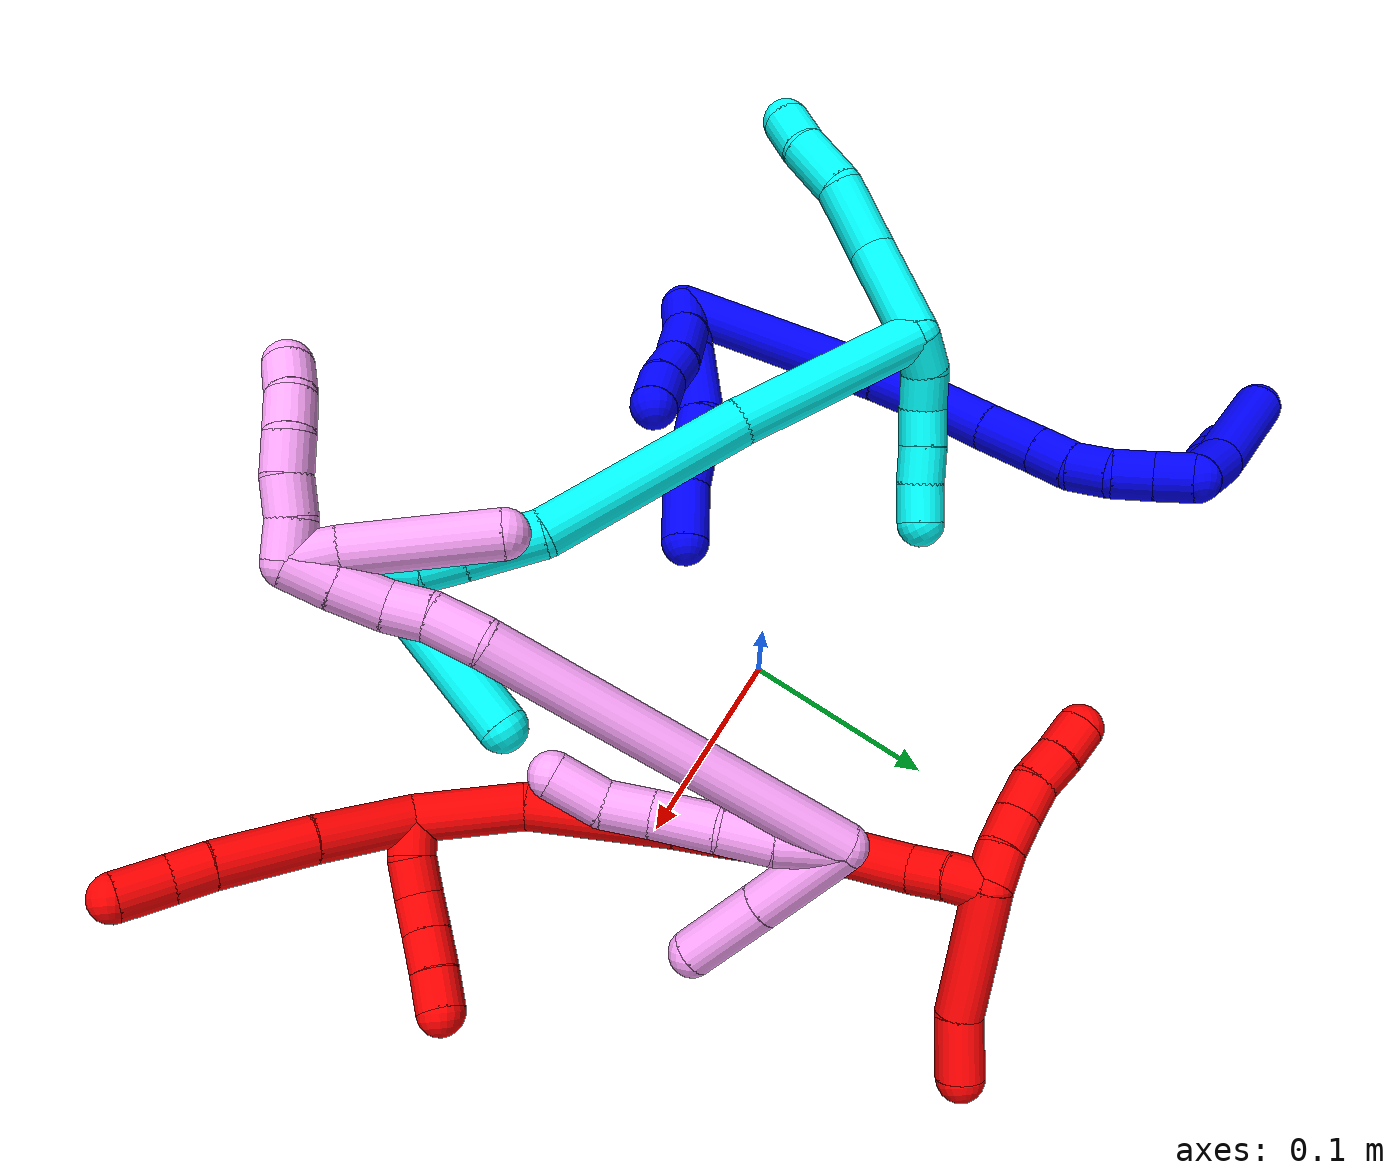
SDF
<sdf version="1.7">
 <world name="default">
  <plugin name="TubeGeneratorPlugin" filename="libtube_generator_plugin.so"/>
  <model name="photoneo_s_sensor">
   <static>1</static>
   <pose>0 0 2 1.57079 1.57079 3.14159</pose>
   <link name="link">
    <inertial><mass>0.1</mass></inertial>
    <sensor name="sensor" type="depth">
     <update_rate>30</update_rate>
     <camera>
      <horizontal_fov>1.22</horizontal_fov>
      <image><width>1920</width><height>1200</height><format>B8G8R8</format></image>
      <clip><near>0.1</near><far>4</far></clip>
      <depth_camera><output>points</output></depth_camera>
     </camera>
     <plugin name="camera_plugin" filename="libgazebo_ros_depth_camera.so">
      <baseline>0.2</baseline>
      <alwaysOn>1</alwaysOn>
      <updateRate>0.0</updateRate>
      <cameraName>camera_ir</cameraName>
      <imageTopicName>/camera/color/image_raw</imageTopicName>
      <cameraInfoTopicName>/camera/color/camera_info</cameraInfoTopicName>
      <depthImageTopicName>/camera/depth/image_raw</depthImageTopicName>
      <depthImageCameraInfoTopicName>/camera/depth/camera_info</depthImageCameraInfoTopicName>
      <pointCloudTopicName>/camera/depth/points</pointCloudTopicName>
      <frameName>fr_optical</frameName>
      <pointCloudCutoff>0.1</pointCloudCutoff>
      <pointCloudCutoffMax>2.0</pointCloudCutoffMax>
      <distortionK1>0</distortionK1>
      <distortionK2>0</distortionK2>
      <distortionK3>0</distortionK3>
      <distortionT1>0</distortionT1>
      <distortionT2>0</distortionT2>
      <CxPrime>0</CxPrime>
      <Cx>0</Cx>
      <Cy>0</Cy>
      <focalLength>0</focalLength>
      <hackBaseline>0</hackBaseline>
     </plugin>
    </sensor>
   </link>
  </model>
  <gravity>0 0 -9.8</gravity>
  <magnetic_field>6e-06 2.3e-05 -4.2e-05</magnetic_field>
  <atmosphere type="adiabatic"/>
  <physics name="default_physics" default="0" type="ode">
   <max_step_size>0.003</max_step_size>
   <real_time_factor>1</real_time_factor>
   <real_time_update_rate>1000</real_time_update_rate>
   <max_contacts>10000</max_contacts>
   <ode>
    <solver>
     <type>quick</type>
     <iters>100</iters>
     <sor>1.3</sor>
     <use_dynamic_moi_rescaling>0</use_dynamic_moi_rescaling>
    </solver>
    <constraints>
     <contact_max_correcting_vel>0</contact_max_correcting_vel>
     <contact_surface_layer>0.001</contact_surface_layer>
     <cfm>0</cfm>
     <erp>0.2</erp>
    </constraints>
   </ode>
  </physics>
  <scene><ambient>0.4 0.4 0.4 1</ambient><background>0.7 0.7 0.7 1</background><shadows>0</shadows></scene>
  <audio><device>default</device></audio>
  <spherical_coordinates>
   <surface_model>EARTH_WGS84</surface_model>
   <latitude_deg>0</latitude_deg>
   <longitude_deg>0</longitude_deg>
   <elevation>0</elevation>
   <heading_deg>0</heading_deg>
  </spherical_coordinates>
  <model name="bin">
   <static>1</static>
   <link name="bottom">
    <collision name="collision-bottom">
     <pose>0 0 -0.01 0 -0 0</pose>
     <geometry><box><size>0.8 0.6 0.02</size></box></geometry>
     <surface>
      <friction><ode><mu>100</mu><mu2>100</mu2></ode></friction>
      <contact><collide_bitmask>65535</collide_bitmask></contact>
     </surface>
    </collision>
   </link>
   <link name="west_wall">
    <collision name="collision-west_wall">
     <pose>-0.41 0 0.1 0 -0 0</pose>
     <geometry><box><size>0.02 0.6 0.2</size></box></geometry>
     <surface>
      <friction><ode><mu>100</mu><mu2>100</mu2></ode></friction>
      <contact><collide_bitmask>65535</collide_bitmask></contact>
     </surface>
    </collision>
   </link>
   <link name="east_wall">
    <collision name="collision-east_wall">
     <pose>0.41 0 0.1 0 -0 0</pose>
     <geometry><box><size>0.02 0.6 0.2</size></box></geometry>
     <surface>
      <friction><ode><mu>100</mu><mu2>100</mu2></ode></friction>
      <contact><collide_bitmask>65535</collide_bitmask></contact>
     </surface>
    </collision>
   </link>
   <link name="south_wall">
    <collision name="collision-south_wall">
     <pose>0 -0.31 0.1 0 -0 0</pose>
     <geometry><box><size>0.8 0.02 0.2</size></box></geometry>
     <surface>
      <friction><ode><mu>100</mu><mu2>100</mu2></ode></friction>
      <contact><collide_bitmask>65535</collide_bitmask></contact>
     </surface>
    </collision>
   </link>
   <link name="north_wall">
    <collision name="collision-north_wall">
     <pose>0 0.31 0.1 0 -0 0</pose>
     <geometry><box><size>0.8 0.02 0.2</size></box></geometry>
     <surface>
      <friction><ode><mu>100</mu><mu2>100</mu2></ode></friction>
      <contact><collide_bitmask>65535</collide_bitmask></contact>
     </surface>
    </collision>
   </link>
  </model>
  <model name="1">
   <static>0</static>
   <link name="1">
    <collision name="collision-cylinder-e_1_2_8">
     <pose>0.001234 0.002123 -0.016681 -3.015 0.073223 -1.04803</pose>
     <geometry><cylinder><radius>0.0125</radius><length>0.033722</length></cylinder></geometry>
     <surface>
      <friction><ode><mu>1.16</mu><mu2>1.16</mu2><slip1>0</slip1><slip2>0</slip2></ode></friction>
      <contact><ode><kp>1e+06</kp><kd>1</kd><max_vel>0</max_vel><min_depth>0.001</min_depth></ode></contact>
     </surface>
    </collision>
    <visual name="visual-cylinder-e_1_2_8">
     <pose>0.001234 0.002123 -0.016681 -3.015 0.073223 -1.04803</pose>
     <geometry><cylinder><radius>0.0125</radius><length>0.033722</length></cylinder></geometry>
     <material><ambient>0 0 1 1</ambient></material>
    </visual>
    <collision name="collision-cylinder-e_2_8_9">
     <pose>0.004088 0.006575 -0.054547 -3.03208 0.07593 -1.21203</pose>
     <geometry><cylinder><radius>0.0125</radius><length>0.042747</length></cylinder></geometry>
     <surface>
      <friction><ode><mu>1.16</mu><mu2>1.16</mu2><slip1>0</slip1><slip2>0</slip2></ode></friction>
      <contact><ode><kp>1e+06</kp><kd>1</kd><max_vel>0</max_vel><min_depth>0.001</min_depth></ode></contact>
     </surface>
    </collision>
    <visual name="visual-cylinder-e_2_8_9">
     <pose>0.004088 0.006575 -0.054547 -3.03208 0.07593 -1.21203</pose>
     <geometry><cylinder><radius>0.0125</radius><length>0.042747</length></cylinder></geometry>
     <material><ambient>0 0 1 1</ambient></material>
    </visual>
    <collision name="collision-cylinder-e_3_9_10">
     <pose>0.007836 0.007129 -0.086274 2.97472 0.196364 1.73373</pose>
     <geometry><cylinder><radius>0.0125</radius><length>0.021802</length></cylinder></geometry>
     <surface>
      <friction><ode><mu>1.16</mu><mu2>1.16</mu2><slip1>0</slip1><slip2>0</slip2></ode></friction>
      <contact><ode><kp>1e+06</kp><kd>1</kd><max_vel>0</max_vel><min_depth>0.001</min_depth></ode></contact>
     </surface>
    </collision>
    <visual name="visual-cylinder-e_3_9_10">
     <pose>0.007836 0.007129 -0.086274 2.97472 0.196364 1.73373</pose>
     <geometry><cylinder><radius>0.0125</radius><length>0.021802</length></cylinder></geometry>
     <material><ambient>0 0 1 1</ambient></material>
    </visual>
    <collision name="collision-cylinder-e_4_10_11">
     <pose>0.010733 0.002442 -0.106555 2.8511 0.075607 0.506049</pose>
     <geometry><cylinder><radius>0.0125</radius><length>0.020386</length></cylinder></geometry>
     <surface>
      <friction><ode><mu>1.16</mu><mu2>1.16</mu2><slip1>0</slip1><slip2>0</slip2></ode></friction>
      <contact><ode><kp>1e+06</kp><kd>1</kd><max_vel>0</max_vel><min_depth>0.001</min_depth></ode></contact>
     </surface>
    </collision>
    <visual name="visual-cylinder-e_4_10_11">
     <pose>0.010733 0.002442 -0.106555 2.8511 0.075607 0.506049</pose>
     <geometry><cylinder><radius>0.0125</radius><length>0.020386</length></cylinder></geometry>
     <material><ambient>0 0 1 1</ambient></material>
    </visual>
    <collision name="collision-cylinder-e_5_11_6">
     <pose>0.011523 -0.002419 -0.131843 3.01688 0.001261 0.02019</pose>
     <geometry><cylinder><radius>0.0125</radius><length>0.031343</length></cylinder></geometry>
     <surface>
      <friction><ode><mu>1.16</mu><mu2>1.16</mu2><slip1>0</slip1><slip2>0</slip2></ode></friction>
      <contact><ode><kp>1e+06</kp><kd>1</kd><max_vel>0</max_vel><min_depth>0.001</min_depth></ode></contact>
     </surface>
    </collision>
    <visual name="visual-cylinder-e_5_11_6">
     <pose>0.011523 -0.002419 -0.131843 3.01688 0.001261 0.02019</pose>
     <geometry><cylinder><radius>0.0125</radius><length>0.031343</length></cylinder></geometry>
     <material><ambient>0 0 1 1</ambient></material>
    </visual>
    <collision name="collision-cylinder-e_1_2_12">
     <pose>0.004422 0.00313 -0.011455 -2.87483 0.356481 -1.86127</pose>
     <geometry><cylinder><radius>0.0125</radius><length>0.025344</length></cylinder></geometry>
     <surface>
      <friction><ode><mu>1.16</mu><mu2>1.16</mu2><slip1>0</slip1><slip2>0</slip2></ode></friction>
      <contact><ode><kp>1e+06</kp><kd>1</kd><max_vel>0</max_vel><min_depth>0.001</min_depth></ode></contact>
     </surface>
    </collision>
    <visual name="visual-cylinder-e_1_2_12">
     <pose>0.004422 0.00313 -0.011455 -2.87483 0.356481 -1.86127</pose>
     <geometry><cylinder><radius>0.0125</radius><length>0.025344</length></cylinder></geometry>
     <material><ambient>0 0 1 1</ambient></material>
    </visual>
    <collision name="collision-cylinder-e_2_12_13">
     <pose>0.016425 0.008169 -0.036508 -3.00218 0.504418 -2.61242</pose>
     <geometry><cylinder><radius>0.0125</radius><length>0.031368</length></cylinder></geometry>
     <surface>
      <friction><ode><mu>1.16</mu><mu2>1.16</mu2><slip1>0</slip1><slip2>0</slip2></ode></friction>
      <contact><ode><kp>1e+06</kp><kd>1</kd><max_vel>0</max_vel><min_depth>0.001</min_depth></ode></contact>
     </surface>
    </collision>
    <visual name="visual-cylinder-e_2_12_13">
     <pose>0.016425 0.008169 -0.036508 -3.00218 0.504418 -2.61242</pose>
     <geometry><cylinder><radius>0.0125</radius><length>0.031368</length></cylinder></geometry>
     <material><ambient>0 0 1 1</ambient></material>
    </visual>
    <collision name="collision-cylinder-e_3_13_14">
     <pose>0.030452 0.00967 -0.058621 3.09381 0.647519 2.99942</pose>
     <geometry><cylinder><radius>0.0125</radius><length>0.021376</length></cylinder></geometry>
     <surface>
      <friction><ode><mu>1.16</mu><mu2>1.16</mu2><slip1>0</slip1><slip2>0</slip2></ode></friction>
      <contact><ode><kp>1e+06</kp><kd>1</kd><max_vel>0</max_vel><min_depth>0.001</min_depth></ode></contact>
     </surface>
    </collision>
    <visual name="visual-cylinder-e_3_13_14">
     <pose>0.030452 0.00967 -0.058621 3.09381 0.647519 2.99942</pose>
     <geometry><cylinder><radius>0.0125</radius><length>0.021376</length></cylinder></geometry>
     <material><ambient>0 0 1 1</ambient></material>
    </visual>
    <collision name="collision-cylinder-e_4_14_5">
     <pose>0.041933 0.009735 -0.076855 -3.09307 0.477416 -2.9428</pose>
     <geometry><cylinder><radius>0.0125</radius><length>0.021912</length></cylinder></geometry>
     <surface>
      <friction><ode><mu>1.16</mu><mu2>1.16</mu2><slip1>0</slip1><slip2>0</slip2></ode></friction>
      <contact><ode><kp>1e+06</kp><kd>1</kd><max_vel>0</max_vel><min_depth>0.001</min_depth></ode></contact>
     </surface>
    </collision>
    <visual name="visual-cylinder-e_4_14_5">
     <pose>0.041933 0.009735 -0.076855 -3.09307 0.477416 -2.9428</pose>
     <geometry><cylinder><radius>0.0125</radius><length>0.021912</length></cylinder></geometry>
     <material><ambient>0 0 1 1</ambient></material>
    </visual>
    <collision name="collision-cylinder-e_1_2_15">
     <pose>-0.026755 0.042532 -0.030605 -2.19453 -0.472097 0.877752</pose>
     <geometry><cylinder><radius>0.0125</radius><length>0.117669</length></cylinder></geometry>
     <surface>
      <friction><ode><mu>1.16</mu><mu2>1.16</mu2><slip1>0</slip1><slip2>0</slip2></ode></friction>
      <contact><ode><kp>1e+06</kp><kd>1</kd><max_vel>0</max_vel><min_depth>0.001</min_depth></ode></contact>
     </surface>
    </collision>
    <visual name="visual-cylinder-e_1_2_15">
     <pose>-0.026755 0.042532 -0.030605 -2.19453 -0.472097 0.877752</pose>
     <geometry><cylinder><radius>0.0125</radius><length>0.117669</length></cylinder></geometry>
     <material><ambient>0 0 1 1</ambient></material>
    </visual>
    <collision name="collision-cylinder-e_2_15_16">
     <pose>-0.060474 0.096439 -0.070464 -2.2538 -0.443386 0.88522</pose>
     <geometry><cylinder><radius>0.0125</radius><length>0.032466</length></cylinder></geometry>
     <surface>
      <friction><ode><mu>1.16</mu><mu2>1.16</mu2><slip1>0</slip1><slip2>0</slip2></ode></friction>
      <contact><ode><kp>1e+06</kp><kd>1</kd><max_vel>0</max_vel><min_depth>0.001</min_depth></ode></contact>
     </surface>
    </collision>
    <visual name="visual-cylinder-e_2_15_16">
     <pose>-0.060474 0.096439 -0.070464 -2.2538 -0.443386 0.88522</pose>
     <geometry><cylinder><radius>0.0125</radius><length>0.032466</length></cylinder></geometry>
     <material><ambient>0 0 1 1</ambient></material>
    </visual>
    <collision name="collision-cylinder-e_3_16_17">
     <pose>-0.072106 0.120261 -0.091287 -2.3196 -0.268064 0.600108</pose>
     <geometry><cylinder><radius>0.0125</radius><length>0.035246</length></cylinder></geometry>
     <surface>
      <friction><ode><mu>1.16</mu><mu2>1.16</mu2><slip1>0</slip1><slip2>0</slip2></ode></friction>
      <contact><ode><kp>1e+06</kp><kd>1</kd><max_vel>0</max_vel><min_depth>0.001</min_depth></ode></contact>
     </surface>
    </collision>
    <visual name="visual-cylinder-e_3_16_17">
     <pose>-0.072106 0.120261 -0.091287 -2.3196 -0.268064 0.600108</pose>
     <geometry><cylinder><radius>0.0125</radius><length>0.035246</length></cylinder></geometry>
     <material><ambient>0 0 1 1</ambient></material>
    </visual>
    <collision name="collision-cylinder-e_4_17_18">
     <pose>-0.079427 0.144408 -0.113592 -2.31331 -0.165537 0.373071</pose>
     <geometry><cylinder><radius>0.0125</radius><length>0.032198</length></cylinder></geometry>
     <surface>
      <friction><ode><mu>1.16</mu><mu2>1.16</mu2><slip1>0</slip1><slip2>0</slip2></ode></friction>
      <contact><ode><kp>1e+06</kp><kd>1</kd><max_vel>0</max_vel><min_depth>0.001</min_depth></ode></contact>
     </surface>
    </collision>
    <visual name="visual-cylinder-e_4_17_18">
     <pose>-0.079427 0.144408 -0.113592 -2.31331 -0.165537 0.373071</pose>
     <geometry><cylinder><radius>0.0125</radius><length>0.032198</length></cylinder></geometry>
     <material><ambient>0 0 1 1</ambient></material>
    </visual>
    <collision name="collision-cylinder-e_5_18_19">
     <pose>-0.083729 0.163463 -0.131228 -2.32417 -0.162067 0.370721</pose>
     <geometry><cylinder><radius>0.0125</radius><length>0.020439</length></cylinder></geometry>
     <surface>
      <friction><ode><mu>1.16</mu><mu2>1.16</mu2><slip1>0</slip1><slip2>0</slip2></ode></friction>
      <contact><ode><kp>1e+06</kp><kd>1</kd><max_vel>0</max_vel><min_depth>0.001</min_depth></ode></contact>
     </surface>
    </collision>
    <visual name="visual-cylinder-e_5_18_19">
     <pose>-0.083729 0.163463 -0.131228 -2.32417 -0.162067 0.370721</pose>
     <geometry><cylinder><radius>0.0125</radius><length>0.020439</length></cylinder></geometry>
     <material><ambient>0 0 1 1</ambient></material>
    </visual>
    <collision name="collision-cylinder-e_6_19_20">
     <pose>-0.087686 0.179511 -0.142829 -2.06666 -0.229466 0.382</pose>
     <geometry><cylinder><radius>0.0125</radius><length>0.020296</length></cylinder></geometry>
     <surface>
      <friction><ode><mu>1.16</mu><mu2>1.16</mu2><slip1>0</slip1><slip2>0</slip2></ode></friction>
      <contact><ode><kp>1e+06</kp><kd>1</kd><max_vel>0</max_vel><min_depth>0.001</min_depth></ode></contact>
     </surface>
    </collision>
    <visual name="visual-cylinder-e_6_19_20">
     <pose>-0.087686 0.179511 -0.142829 -2.06666 -0.229466 0.382</pose>
     <geometry><cylinder><radius>0.0125</radius><length>0.020296</length></cylinder></geometry>
     <material><ambient>0 0 1 1</ambient></material>
    </visual>
    <collision name="collision-cylinder-e_7_20_21">
     <pose>-0.094872 0.19724 -0.150149 -1.85282 -0.478321 0.62757</pose>
     <geometry><cylinder><radius>0.0125</radius><length>0.021196</length></cylinder></geometry>
     <surface>
      <friction><ode><mu>1.16</mu><mu2>1.16</mu2><slip1>0</slip1><slip2>0</slip2></ode></friction>
      <contact><ode><kp>1e+06</kp><kd>1</kd><max_vel>0</max_vel><min_depth>0.001</min_depth></ode></contact>
     </surface>
    </collision>
    <visual name="visual-cylinder-e_7_20_21">
     <pose>-0.094872 0.19724 -0.150149 -1.85282 -0.478321 0.62757</pose>
     <geometry><cylinder><radius>0.0125</radius><length>0.021196</length></cylinder></geometry>
     <material><ambient>0 0 1 1</ambient></material>
    </visual>
    <collision name="collision-cylinder-e_8_21_1">
     <pose>-0.102668 0.215593 -0.155873 -1.89258 -0.288789 0.398151</pose>
     <geometry><cylinder><radius>0.0125</radius><length>0.020491</length></cylinder></geometry>
     <surface>
      <friction><ode><mu>1.16</mu><mu2>1.16</mu2><slip1>0</slip1><slip2>0</slip2></ode></friction>
      <contact><ode><kp>1e+06</kp><kd>1</kd><max_vel>0</max_vel><min_depth>0.001</min_depth></ode></contact>
     </surface>
    </collision>
    <visual name="visual-cylinder-e_8_21_1">
     <pose>-0.102668 0.215593 -0.155873 -1.89258 -0.288789 0.398151</pose>
     <geometry><cylinder><radius>0.0125</radius><length>0.020491</length></cylinder></geometry>
     <material><ambient>0 0 1 1</ambient></material>
    </visual>
    <collision name="collision-cylinder-e_1_1_22">
     <pose>-0.123408 0.221867 -0.14792 0.268562 -0.998954 -0.147155</pose>
     <geometry><cylinder><radius>0.0125</radius><length>0.042389</length></cylinder></geometry>
     <surface>
      <friction><ode><mu>1.16</mu><mu2>1.16</mu2><slip1>0</slip1><slip2>0</slip2></ode></friction>
      <contact><ode><kp>1e+06</kp><kd>1</kd><max_vel>0</max_vel><min_depth>0.001</min_depth></ode></contact>
     </surface>
    </collision>
    <visual name="visual-cylinder-e_1_1_22">
     <pose>-0.123408 0.221867 -0.14792 0.268562 -0.998954 -0.147155</pose>
     <geometry><cylinder><radius>0.0125</radius><length>0.042389</length></cylinder></geometry>
     <material><ambient>0 0 1 1</ambient></material>
    </visual>
    <collision name="collision-cylinder-e_2_22_23">
     <pose>-0.150432 0.217934 -0.13052 0.139313 -0.962796 -0.072861</pose>
     <geometry><cylinder><radius>0.0125</radius><length>0.02242</length></cylinder></geometry>
     <surface>
      <friction><ode><mu>1.16</mu><mu2>1.16</mu2><slip1>0</slip1><slip2>0</slip2></ode></friction>
      <contact><ode><kp>1e+06</kp><kd>1</kd><max_vel>0</max_vel><min_depth>0.001</min_depth></ode></contact>
     </surface>
    </collision>
    <visual name="visual-cylinder-e_2_22_23">
     <pose>-0.150432 0.217934 -0.13052 0.139313 -0.962796 -0.072861</pose>
     <geometry><cylinder><radius>0.0125</radius><length>0.02242</length></cylinder></geometry>
     <material><ambient>0 0 1 1</ambient></material>
    </visual>
    <collision name="collision-cylinder-e_3_23_4">
     <pose>-0.174319 0.215922 -0.114552 0.11613 -0.98746 -0.06255</pose>
     <geometry><cylinder><radius>0.0125</radius><length>0.03519</length></cylinder></geometry>
     <surface>
      <friction><ode><mu>1.16</mu><mu2>1.16</mu2><slip1>0</slip1><slip2>0</slip2></ode></friction>
      <contact><ode><kp>1e+06</kp><kd>1</kd><max_vel>0</max_vel><min_depth>0.001</min_depth></ode></contact>
     </surface>
    </collision>
    <visual name="visual-cylinder-e_3_23_4">
     <pose>-0.174319 0.215922 -0.114552 0.11613 -0.98746 -0.06255</pose>
     <geometry><cylinder><radius>0.0125</radius><length>0.03519</length></cylinder></geometry>
     <material><ambient>0 0 1 1</ambient></material>
    </visual>
    <collision name="collision-cylinder-e_1_1_24">
     <pose>-0.116932 0.227245 -0.151166 -0.290398 -0.947637 0.149685</pose>
     <geometry><cylinder><radius>0.0125</radius><length>0.027946</length></cylinder></geometry>
     <surface>
      <friction><ode><mu>1.16</mu><mu2>1.16</mu2><slip1>0</slip1><slip2>0</slip2></ode></friction>
      <contact><ode><kp>1e+06</kp><kd>1</kd><max_vel>0</max_vel><min_depth>0.001</min_depth></ode></contact>
     </surface>
    </collision>
    <visual name="visual-cylinder-e_1_1_24">
     <pose>-0.116932 0.227245 -0.151166 -0.290398 -0.947637 0.149685</pose>
     <geometry><cylinder><radius>0.0125</radius><length>0.027946</length></cylinder></geometry>
     <material><ambient>0 0 1 1</ambient></material>
    </visual>
    <collision name="collision-cylinder-e_2_24_3">
     <pose>-0.154402 0.23502 -0.119147 -0.22106 -0.811176 0.095239</pose>
     <geometry><cylinder><radius>0.0125</radius><length>0.072054</length></cylinder></geometry>
     <surface>
      <friction><ode><mu>1.16</mu><mu2>1.16</mu2><slip1>0</slip1><slip2>0</slip2></ode></friction>
      <contact><ode><kp>1e+06</kp><kd>1</kd><max_vel>0</max_vel><min_depth>0.001</min_depth></ode></contact>
     </surface>
    </collision>
    <visual name="visual-cylinder-e_2_24_3">
     <pose>-0.154402 0.23502 -0.119147 -0.22106 -0.811176 0.095239</pose>
     <geometry><cylinder><radius>0.0125</radius><length>0.072054</length></cylinder></geometry>
     <material><ambient>0 0 1 1</ambient></material>
    </visual>
    <collision name="collision-sphere-3">
     <pose>-0.180525 0.24046 -0.094941 0 -0 0</pose>
     <geometry><sphere><radius>0.0125</radius></sphere></geometry>
     <surface>
      <friction><ode><mu>1.16</mu><mu2>1.16</mu2><slip1>0</slip1><slip2>0</slip2></ode></friction>
      <contact><ode><kp>1e+06</kp><kd>1</kd><max_vel>0</max_vel><min_depth>0.001</min_depth></ode></contact>
     </surface>
    </collision>
    <visual name="visual-sphere-3">
     <pose>-0.180525 0.24046 -0.094941 0 -0 0</pose>
     <geometry><sphere><radius>0.0125</radius></sphere></geometry>
     <material><ambient>0 0 1 1</ambient></material>
    </visual>
    <collision name="collision-sphere-24">
     <pose>-0.128279 0.22958 -0.143353 0 -0 0</pose>
     <geometry><sphere><radius>0.0125</radius></sphere></geometry>
     <surface>
      <friction><ode><mu>1.16</mu><mu2>1.16</mu2><slip1>0</slip1><slip2>0</slip2></ode></friction>
      <contact><ode><kp>1e+06</kp><kd>1</kd><max_vel>0</max_vel><min_depth>0.001</min_depth></ode></contact>
     </surface>
    </collision>
    <visual name="visual-sphere-24">
     <pose>-0.128279 0.22958 -0.143353 0 -0 0</pose>
     <geometry><sphere><radius>0.0125</radius></sphere></geometry>
     <material><ambient>0 0 1 1</ambient></material>
    </visual>
    <collision name="collision-sphere-4">
     <pose>-0.189005 0.214799 -0.104926 0 -0 0</pose>
     <geometry><sphere><radius>0.0125</radius></sphere></geometry>
     <surface>
      <friction><ode><mu>1.16</mu><mu2>1.16</mu2><slip1>0</slip1><slip2>0</slip2></ode></friction>
      <contact><ode><kp>1e+06</kp><kd>1</kd><max_vel>0</max_vel><min_depth>0.001</min_depth></ode></contact>
     </surface>
    </collision>
    <visual name="visual-sphere-4">
     <pose>-0.189005 0.214799 -0.104926 0 -0 0</pose>
     <geometry><sphere><radius>0.0125</radius></sphere></geometry>
     <material><ambient>0 0 1 1</ambient></material>
    </visual>
    <collision name="collision-sphere-23">
     <pose>-0.159634 0.217045 -0.124178 0 -0 0</pose>
     <geometry><sphere><radius>0.0125</radius></sphere></geometry>
     <surface>
      <friction><ode><mu>1.16</mu><mu2>1.16</mu2><slip1>0</slip1><slip2>0</slip2></ode></friction>
      <contact><ode><kp>1e+06</kp><kd>1</kd><max_vel>0</max_vel><min_depth>0.001</min_depth></ode></contact>
     </surface>
    </collision>
    <visual name="visual-sphere-23">
     <pose>-0.159634 0.217045 -0.124178 0 -0 0</pose>
     <geometry><sphere><radius>0.0125</radius></sphere></geometry>
     <material><ambient>0 0 1 1</ambient></material>
    </visual>
    <collision name="collision-sphere-22">
     <pose>-0.141231 0.218823 -0.136862 0 -0 0</pose>
     <geometry><sphere><radius>0.0125</radius></sphere></geometry>
     <surface>
      <friction><ode><mu>1.16</mu><mu2>1.16</mu2><slip1>0</slip1><slip2>0</slip2></ode></friction>
      <contact><ode><kp>1e+06</kp><kd>1</kd><max_vel>0</max_vel><min_depth>0.001</min_depth></ode></contact>
     </surface>
    </collision>
    <visual name="visual-sphere-22">
     <pose>-0.141231 0.218823 -0.136862 0 -0 0</pose>
     <geometry><sphere><radius>0.0125</radius></sphere></geometry>
     <material><ambient>0 0 1 1</ambient></material>
    </visual>
    <collision name="collision-sphere-1">
     <pose>-0.105586 0.22491 -0.158979 0 -0 0</pose>
     <geometry><sphere><radius>0.0125</radius></sphere></geometry>
     <surface>
      <friction><ode><mu>1.16</mu><mu2>1.16</mu2><slip1>0</slip1><slip2>0</slip2></ode></friction>
      <contact><ode><kp>1e+06</kp><kd>1</kd><max_vel>0</max_vel><min_depth>0.001</min_depth></ode></contact>
     </surface>
    </collision>
    <visual name="visual-sphere-1">
     <pose>-0.105586 0.22491 -0.158979 0 -0 0</pose>
     <geometry><sphere><radius>0.0125</radius></sphere></geometry>
     <material><ambient>0 0 1 1</ambient></material>
    </visual>
    <collision name="collision-sphere-21">
     <pose>-0.09975 0.206277 -0.152767 0 -0 0</pose>
     <geometry><sphere><radius>0.0125</radius></sphere></geometry>
     <surface>
      <friction><ode><mu>1.16</mu><mu2>1.16</mu2><slip1>0</slip1><slip2>0</slip2></ode></friction>
      <contact><ode><kp>1e+06</kp><kd>1</kd><max_vel>0</max_vel><min_depth>0.001</min_depth></ode></contact>
     </surface>
    </collision>
    <visual name="visual-sphere-21">
     <pose>-0.09975 0.206277 -0.152767 0 -0 0</pose>
     <geometry><sphere><radius>0.0125</radius></sphere></geometry>
     <material><ambient>0 0 1 1</ambient></material>
    </visual>
    <collision name="collision-sphere-6">
     <pose>0.011543 -0.004368 -0.147393 0 -0 0</pose>
     <geometry><sphere><radius>0.0125</radius></sphere></geometry>
     <surface>
      <friction><ode><mu>1.16</mu><mu2>1.16</mu2><slip1>0</slip1><slip2>0</slip2></ode></friction>
      <contact><ode><kp>1e+06</kp><kd>1</kd><max_vel>0</max_vel><min_depth>0.001</min_depth></ode></contact>
     </surface>
    </collision>
    <visual name="visual-sphere-6">
     <pose>0.011543 -0.004368 -0.147393 0 -0 0</pose>
     <geometry><sphere><radius>0.0125</radius></sphere></geometry>
     <material><ambient>0 0 1 1</ambient></material>
    </visual>
    <collision name="collision-sphere-11">
     <pose>0.011503 -0.000469 -0.116293 0 -0 0</pose>
     <geometry><sphere><radius>0.0125</radius></sphere></geometry>
     <surface>
      <friction><ode><mu>1.16</mu><mu2>1.16</mu2><slip1>0</slip1><slip2>0</slip2></ode></friction>
      <contact><ode><kp>1e+06</kp><kd>1</kd><max_vel>0</max_vel><min_depth>0.001</min_depth></ode></contact>
     </surface>
    </collision>
    <visual name="visual-sphere-11">
     <pose>0.011503 -0.000469 -0.116293 0 -0 0</pose>
     <geometry><sphere><radius>0.0125</radius></sphere></geometry>
     <material><ambient>0 0 1 1</ambient></material>
    </visual>
    <collision name="collision-sphere-10">
     <pose>0.009963 0.005353 -0.096817 0 -0 0</pose>
     <geometry><sphere><radius>0.0125</radius></sphere></geometry>
     <surface>
      <friction><ode><mu>1.16</mu><mu2>1.16</mu2><slip1>0</slip1><slip2>0</slip2></ode></friction>
      <contact><ode><kp>1e+06</kp><kd>1</kd><max_vel>0</max_vel><min_depth>0.001</min_depth></ode></contact>
     </surface>
    </collision>
    <visual name="visual-sphere-10">
     <pose>0.009963 0.005353 -0.096817 0 -0 0</pose>
     <geometry><sphere><radius>0.0125</radius></sphere></geometry>
     <material><ambient>0 0 1 1</ambient></material>
    </visual>
    <collision name="collision-sphere-9">
     <pose>0.00571 0.008905 -0.075731 0 -0 0</pose>
     <geometry><sphere><radius>0.0125</radius></sphere></geometry>
     <surface>
      <friction><ode><mu>1.16</mu><mu2>1.16</mu2><slip1>0</slip1><slip2>0</slip2></ode></friction>
      <contact><ode><kp>1e+06</kp><kd>1</kd><max_vel>0</max_vel><min_depth>0.001</min_depth></ode></contact>
     </surface>
    </collision>
    <visual name="visual-sphere-9">
     <pose>0.00571 0.008905 -0.075731 0 -0 0</pose>
     <geometry><sphere><radius>0.0125</radius></sphere></geometry>
     <material><ambient>0 0 1 1</ambient></material>
    </visual>
    <collision name="collision-sphere-2">
     <geometry><sphere><radius>0.0125</radius></sphere></geometry>
     <surface>
      <friction><ode><mu>1.16</mu><mu2>1.16</mu2><slip1>0</slip1><slip2>0</slip2></ode></friction>
      <contact><ode><kp>1e+06</kp><kd>1</kd><max_vel>0</max_vel><min_depth>0.001</min_depth></ode></contact>
     </surface>
    </collision>
    <visual name="visual-sphere-2">
     <geometry><sphere><radius>0.0125</radius></sphere></geometry>
     <material><ambient>0 0 1 1</ambient></material>
    </visual>
    <collision name="collision-sphere-19">
     <pose>-0.085378 0.170819 -0.138127 0 -0 0</pose>
     <geometry><sphere><radius>0.0125</radius></sphere></geometry>
     <surface>
      <friction><ode><mu>1.16</mu><mu2>1.16</mu2><slip1>0</slip1><slip2>0</slip2></ode></friction>
      <contact><ode><kp>1e+06</kp><kd>1</kd><max_vel>0</max_vel><min_depth>0.001</min_depth></ode></contact>
     </surface>
    </collision>
    <visual name="visual-sphere-19">
     <pose>-0.085378 0.170819 -0.138127 0 -0 0</pose>
     <geometry><sphere><radius>0.0125</radius></sphere></geometry>
     <material><ambient>0 0 1 1</ambient></material>
    </visual>
    <collision name="collision-sphere-8">
     <pose>0.002467 0.004246 -0.033363 0 -0 0</pose>
     <geometry><sphere><radius>0.0125</radius></sphere></geometry>
     <surface>
      <friction><ode><mu>1.16</mu><mu2>1.16</mu2><slip1>0</slip1><slip2>0</slip2></ode></friction>
      <contact><ode><kp>1e+06</kp><kd>1</kd><max_vel>0</max_vel><min_depth>0.001</min_depth></ode></contact>
     </surface>
    </collision>
    <visual name="visual-sphere-8">
     <pose>0.002467 0.004246 -0.033363 0 -0 0</pose>
     <geometry><sphere><radius>0.0125</radius></sphere></geometry>
     <material><ambient>0 0 1 1</ambient></material>
    </visual>
    <collision name="collision-sphere-12">
     <pose>0.008845 0.006261 -0.022911 0 -0 0</pose>
     <geometry><sphere><radius>0.0125</radius></sphere></geometry>
     <surface>
      <friction><ode><mu>1.16</mu><mu2>1.16</mu2><slip1>0</slip1><slip2>0</slip2></ode></friction>
      <contact><ode><kp>1e+06</kp><kd>1</kd><max_vel>0</max_vel><min_depth>0.001</min_depth></ode></contact>
     </surface>
    </collision>
    <visual name="visual-sphere-12">
     <pose>0.008845 0.006261 -0.022911 0 -0 0</pose>
     <geometry><sphere><radius>0.0125</radius></sphere></geometry>
     <material><ambient>0 0 1 1</ambient></material>
    </visual>
    <collision name="collision-sphere-13">
     <pose>0.024005 0.010077 -0.050106 0 -0 0</pose>
     <geometry><sphere><radius>0.0125</radius></sphere></geometry>
     <surface>
      <friction><ode><mu>1.16</mu><mu2>1.16</mu2><slip1>0</slip1><slip2>0</slip2></ode></friction>
      <contact><ode><kp>1e+06</kp><kd>1</kd><max_vel>0</max_vel><min_depth>0.001</min_depth></ode></contact>
     </surface>
    </collision>
    <visual name="visual-sphere-13">
     <pose>0.024005 0.010077 -0.050106 0 -0 0</pose>
     <geometry><sphere><radius>0.0125</radius></sphere></geometry>
     <material><ambient>0 0 1 1</ambient></material>
    </visual>
    <collision name="collision-sphere-14">
     <pose>0.036899 0.009263 -0.067135 0 -0 0</pose>
     <geometry><sphere><radius>0.0125</radius></sphere></geometry>
     <surface>
      <friction><ode><mu>1.16</mu><mu2>1.16</mu2><slip1>0</slip1><slip2>0</slip2></ode></friction>
      <contact><ode><kp>1e+06</kp><kd>1</kd><max_vel>0</max_vel><min_depth>0.001</min_depth></ode></contact>
     </surface>
    </collision>
    <visual name="visual-sphere-14">
     <pose>0.036899 0.009263 -0.067135 0 -0 0</pose>
     <geometry><sphere><radius>0.0125</radius></sphere></geometry>
     <material><ambient>0 0 1 1</ambient></material>
    </visual>
    <collision name="collision-sphere-5">
     <pose>0.046967 0.010207 -0.086574 0 -0 0</pose>
     <geometry><sphere><radius>0.0125</radius></sphere></geometry>
     <surface>
      <friction><ode><mu>1.16</mu><mu2>1.16</mu2><slip1>0</slip1><slip2>0</slip2></ode></friction>
      <contact><ode><kp>1e+06</kp><kd>1</kd><max_vel>0</max_vel><min_depth>0.001</min_depth></ode></contact>
     </surface>
    </collision>
    <visual name="visual-sphere-5">
     <pose>0.046967 0.010207 -0.086574 0 -0 0</pose>
     <geometry><sphere><radius>0.0125</radius></sphere></geometry>
     <material><ambient>0 0 1 1</ambient></material>
    </visual>
    <collision name="collision-sphere-15">
     <pose>-0.05351 0.085065 -0.061209 0 -0 0</pose>
     <geometry><sphere><radius>0.0125</radius></sphere></geometry>
     <surface>
      <friction><ode><mu>1.16</mu><mu2>1.16</mu2><slip1>0</slip1><slip2>0</slip2></ode></friction>
      <contact><ode><kp>1e+06</kp><kd>1</kd><max_vel>0</max_vel><min_depth>0.001</min_depth></ode></contact>
     </surface>
    </collision>
    <visual name="visual-sphere-15">
     <pose>-0.05351 0.085065 -0.061209 0 -0 0</pose>
     <geometry><sphere><radius>0.0125</radius></sphere></geometry>
     <material><ambient>0 0 1 1</ambient></material>
    </visual>
    <collision name="collision-sphere-16">
     <pose>-0.067438 0.107813 -0.079718 0 -0 0</pose>
     <geometry><sphere><radius>0.0125</radius></sphere></geometry>
     <surface>
      <friction><ode><mu>1.16</mu><mu2>1.16</mu2><slip1>0</slip1><slip2>0</slip2></ode></friction>
      <contact><ode><kp>1e+06</kp><kd>1</kd><max_vel>0</max_vel><min_depth>0.001</min_depth></ode></contact>
     </surface>
    </collision>
    <visual name="visual-sphere-16">
     <pose>-0.067438 0.107813 -0.079718 0 -0 0</pose>
     <geometry><sphere><radius>0.0125</radius></sphere></geometry>
     <material><ambient>0 0 1 1</ambient></material>
    </visual>
    <collision name="collision-sphere-17">
     <pose>-0.076774 0.132709 -0.102855 0 -0 0</pose>
     <geometry><sphere><radius>0.0125</radius></sphere></geometry>
     <surface>
      <friction><ode><mu>1.16</mu><mu2>1.16</mu2><slip1>0</slip1><slip2>0</slip2></ode></friction>
      <contact><ode><kp>1e+06</kp><kd>1</kd><max_vel>0</max_vel><min_depth>0.001</min_depth></ode></contact>
     </surface>
    </collision>
    <visual name="visual-sphere-17">
     <pose>-0.076774 0.132709 -0.102855 0 -0 0</pose>
     <geometry><sphere><radius>0.0125</radius></sphere></geometry>
     <material><ambient>0 0 1 1</ambient></material>
    </visual>
    <collision name="collision-sphere-18">
     <pose>-0.08208 0.156107 -0.124328 0 -0 0</pose>
     <geometry><sphere><radius>0.0125</radius></sphere></geometry>
     <surface>
      <friction><ode><mu>1.16</mu><mu2>1.16</mu2><slip1>0</slip1><slip2>0</slip2></ode></friction>
      <contact><ode><kp>1e+06</kp><kd>1</kd><max_vel>0</max_vel><min_depth>0.001</min_depth></ode></contact>
     </surface>
    </collision>
    <visual name="visual-sphere-18">
     <pose>-0.08208 0.156107 -0.124328 0 -0 0</pose>
     <geometry><sphere><radius>0.0125</radius></sphere></geometry>
     <material><ambient>0 0 1 1</ambient></material>
    </visual>
    <collision name="collision-sphere-20">
     <pose>-0.089994 0.188203 -0.147531 0 -0 0</pose>
     <geometry><sphere><radius>0.0125</radius></sphere></geometry>
     <surface>
      <friction><ode><mu>1.16</mu><mu2>1.16</mu2><slip1>0</slip1><slip2>0</slip2></ode></friction>
      <contact><ode><kp>1e+06</kp><kd>1</kd><max_vel>0</max_vel><min_depth>0.001</min_depth></ode></contact>
     </surface>
    </collision>
    <visual name="visual-sphere-20">
     <pose>-0.089994 0.188203 -0.147531 0 -0 0</pose>
     <geometry><sphere><radius>0.0125</radius></sphere></geometry>
     <material><ambient>0 0 1 1</ambient></material>
    </visual>
    <inertial>
     <pose>-0.058378 0.105358 -0.088281 0 -0 0</pose>
     <mass>0.75</mass>
     <inertia><ixx>0.00021</ixx><ixy>0</ixy><ixz>0</ixz><iyy>0.000142</iyy><iyz>0</iyz><izz>-4e-05</izz></inertia>
    </inertial>
   </link>
   <pose>-0.148937 -0.143434 0.011495 1.87476 -0.896264 -1.15377</pose>
  </model>
  <model name="2">
   <static>0</static>
   <link name="2">
    <collision name="collision-cylinder-e_1_2_8">
     <pose>0.005682 -0.025695 0.003774 1.42496 0.215406 0.186262</pose>
     <geometry><cylinder><radius>0.0125</radius><length>0.05317</length></cylinder></geometry>
     <surface>
      <friction><ode><mu>1.16</mu><mu2>1.16</mu2><slip1>0</slip1><slip2>0</slip2></ode></friction>
      <contact><ode><kp>1e+06</kp><kd>1</kd><max_vel>0</max_vel><min_depth>0.001</min_depth></ode></contact>
     </surface>
    </collision>
    <visual name="visual-cylinder-e_1_2_8">
     <pose>0.005682 -0.025695 0.003774 1.42496 0.215406 0.186262</pose>
     <geometry><cylinder><radius>0.0125</radius><length>0.05317</length></cylinder></geometry>
     <material><ambient>1 0 0 1</ambient></material>
    </visual>
    <collision name="collision-cylinder-e_2_8_9">
     <pose>0.018055 -0.075103 0.012099 1.38119 0.270286 0.223779</pose>
     <geometry><cylinder><radius>0.0125</radius><length>0.050112</length></cylinder></geometry>
     <surface>
      <friction><ode><mu>1.16</mu><mu2>1.16</mu2><slip1>0</slip1><slip2>0</slip2></ode></friction>
      <contact><ode><kp>1e+06</kp><kd>1</kd><max_vel>0</max_vel><min_depth>0.001</min_depth></ode></contact>
     </surface>
    </collision>
    <visual name="visual-cylinder-e_2_8_9">
     <pose>0.018055 -0.075103 0.012099 1.38119 0.270286 0.223779</pose>
     <geometry><cylinder><radius>0.0125</radius><length>0.050112</length></cylinder></geometry>
     <material><ambient>1 0 0 1</ambient></material>
    </visual>
    <collision name="collision-cylinder-e_3_9_10">
     <pose>0.027709 -0.108087 0.019133 1.30908 0.299561 0.230588</pose>
     <geometry><cylinder><radius>0.0125</radius><length>0.020088</length></cylinder></geometry>
     <surface>
      <friction><ode><mu>1.16</mu><mu2>1.16</mu2><slip1>0</slip1><slip2>0</slip2></ode></friction>
      <contact><ode><kp>1e+06</kp><kd>1</kd><max_vel>0</max_vel><min_depth>0.001</min_depth></ode></contact>
     </surface>
    </collision>
    <visual name="visual-cylinder-e_3_9_10">
     <pose>0.027709 -0.108087 0.019133 1.30908 0.299561 0.230588</pose>
     <geometry><cylinder><radius>0.0125</radius><length>0.020088</length></cylinder></geometry>
     <material><ambient>1 0 0 1</ambient></material>
    </visual>
    <collision name="collision-cylinder-e_4_10_6">
     <pose>0.033957 -0.129847 0.024857 1.31691 0.249211 0.1932</pose>
     <geometry><cylinder><radius>0.0125</radius><length>0.02663</length></cylinder></geometry>
     <surface>
      <friction><ode><mu>1.16</mu><mu2>1.16</mu2><slip1>0</slip1><slip2>0</slip2></ode></friction>
      <contact><ode><kp>1e+06</kp><kd>1</kd><max_vel>0</max_vel><min_depth>0.001</min_depth></ode></contact>
     </surface>
    </collision>
    <visual name="visual-cylinder-e_4_10_6">
     <pose>0.033957 -0.129847 0.024857 1.31691 0.249211 0.1932</pose>
     <geometry><cylinder><radius>0.0125</radius><length>0.02663</length></cylinder></geometry>
     <material><ambient>1 0 0 1</ambient></material>
    </visual>
    <collision name="collision-cylinder-e_1_2_11">
     <pose>-7.8e-05 -0.00122 0.009925 0.122263 -0.007815 -0.000478</pose>
     <geometry><cylinder><radius>0.0125</radius><length>0.02</length></cylinder></geometry>
     <surface>
      <friction><ode><mu>1.16</mu><mu2>1.16</mu2><slip1>0</slip1><slip2>0</slip2></ode></friction>
      <contact><ode><kp>1e+06</kp><kd>1</kd><max_vel>0</max_vel><min_depth>0.001</min_depth></ode></contact>
     </surface>
    </collision>
    <visual name="visual-cylinder-e_1_2_11">
     <pose>-7.8e-05 -0.00122 0.009925 0.122263 -0.007815 -0.000478</pose>
     <geometry><cylinder><radius>0.0125</radius><length>0.02</length></cylinder></geometry>
     <material><ambient>1 0 0 1</ambient></material>
    </visual>
    <collision name="collision-cylinder-e_2_11_12">
     <pose>-0.000547 -0.001127 0.029756 -0.131706 -0.039087 0.002578</pose>
     <geometry><cylinder><radius>0.0125</radius><length>0.02</length></cylinder></geometry>
     <surface>
      <friction><ode><mu>1.16</mu><mu2>1.16</mu2><slip1>0</slip1><slip2>0</slip2></ode></friction>
      <contact><ode><kp>1e+06</kp><kd>1</kd><max_vel>0</max_vel><min_depth>0.001</min_depth></ode></contact>
     </surface>
    </collision>
    <visual name="visual-cylinder-e_2_11_12">
     <pose>-0.000547 -0.001127 0.029756 -0.131706 -0.039087 0.002578</pose>
     <geometry><cylinder><radius>0.0125</radius><length>0.02</length></cylinder></geometry>
     <material><ambient>1 0 0 1</ambient></material>
    </visual>
    <collision name="collision-cylinder-e_3_12_13">
     <pose>-0.004133 -9.7e-05 0.049133 0.029759 -0.325255 -0.004883</pose>
     <geometry><cylinder><radius>0.0125</radius><length>0.02</length></cylinder></geometry>
     <surface>
      <friction><ode><mu>1.16</mu><mu2>1.16</mu2><slip1>0</slip1><slip2>0</slip2></ode></friction>
      <contact><ode><kp>1e+06</kp><kd>1</kd><max_vel>0</max_vel><min_depth>0.001</min_depth></ode></contact>
     </surface>
    </collision>
    <visual name="visual-cylinder-e_3_12_13">
     <pose>-0.004133 -9.7e-05 0.049133 0.029759 -0.325255 -0.004883</pose>
     <geometry><cylinder><radius>0.0125</radius><length>0.02</length></cylinder></geometry>
     <material><ambient>1 0 0 1</ambient></material>
    </visual>
    <collision name="collision-cylinder-e_4_13_14">
     <pose>-0.010527 -0.000784 0.068071 0.042839 -0.325533 -0.007036</pose>
     <geometry><cylinder><radius>0.0125</radius><length>0.02</length></cylinder></geometry>
     <surface>
      <friction><ode><mu>1.16</mu><mu2>1.16</mu2><slip1>0</slip1><slip2>0</slip2></ode></friction>
      <contact><ode><kp>1e+06</kp><kd>1</kd><max_vel>0</max_vel><min_depth>0.001</min_depth></ode></contact>
     </surface>
    </collision>
    <visual name="visual-cylinder-e_4_13_14">
     <pose>-0.010527 -0.000784 0.068071 0.042839 -0.325533 -0.007036</pose>
     <geometry><cylinder><radius>0.0125</radius><length>0.02</length></cylinder></geometry>
     <material><ambient>1 0 0 1</ambient></material>
    </visual>
    <collision name="collision-cylinder-e_5_14_5">
     <pose>-0.016317 -0.00156 0.087188 0.038268 -0.262193 -0.005046</pose>
     <geometry><cylinder><radius>0.0125</radius><length>0.02</length></cylinder></geometry>
     <surface>
      <friction><ode><mu>1.16</mu><mu2>1.16</mu2><slip1>0</slip1><slip2>0</slip2></ode></friction>
      <contact><ode><kp>1e+06</kp><kd>1</kd><max_vel>0</max_vel><min_depth>0.001</min_depth></ode></contact>
     </surface>
    </collision>
    <visual name="visual-cylinder-e_5_14_5">
     <pose>-0.016317 -0.00156 0.087188 0.038268 -0.262193 -0.005046</pose>
     <geometry><cylinder><radius>0.0125</radius><length>0.02</length></cylinder></geometry>
     <material><ambient>1 0 0 1</ambient></material>
    </visual>
    <collision name="collision-cylinder-e_1_2_15">
     <pose>-0.01921 0.021788 -0.000707 -1.60324 -0.722342 0.744056</pose>
     <geometry><cylinder><radius>0.0125</radius><length>0.058111</length></cylinder></geometry>
     <surface>
      <friction><ode><mu>1.16</mu><mu2>1.16</mu2><slip1>0</slip1><slip2>0</slip2></ode></friction>
      <contact><ode><kp>1e+06</kp><kd>1</kd><max_vel>0</max_vel><min_depth>0.001</min_depth></ode></contact>
     </surface>
    </collision>
    <visual name="visual-cylinder-e_1_2_15">
     <pose>-0.01921 0.021788 -0.000707 -1.60324 -0.722342 0.744056</pose>
     <geometry><cylinder><radius>0.0125</radius><length>0.058111</length></cylinder></geometry>
     <material><ambient>1 0 0 1</ambient></material>
    </visual>
    <collision name="collision-cylinder-e_2_15_16">
     <pose>-0.063163 0.07223 0.006608 -1.29783 -0.693684 0.535169</pose>
     <geometry><cylinder><radius>0.0125</radius><length>0.077399</length></cylinder></geometry>
     <surface>
      <friction><ode><mu>1.16</mu><mu2>1.16</mu2><slip1>0</slip1><slip2>0</slip2></ode></friction>
      <contact><ode><kp>1e+06</kp><kd>1</kd><max_vel>0</max_vel><min_depth>0.001</min_depth></ode></contact>
     </surface>
    </collision>
    <visual name="visual-cylinder-e_2_15_16">
     <pose>-0.063163 0.07223 0.006608 -1.29783 -0.693684 0.535169</pose>
     <geometry><cylinder><radius>0.0125</radius><length>0.077399</length></cylinder></geometry>
     <material><ambient>1 0 0 1</ambient></material>
    </visual>
    <collision name="collision-cylinder-e_3_16_17">
     <pose>-0.096561 0.109752 0.017913 -1.21618 -0.741129 0.528237</pose>
     <geometry><cylinder><radius>0.0125</radius><length>0.025636</length></cylinder></geometry>
     <surface>
      <friction><ode><mu>1.16</mu><mu2>1.16</mu2><slip1>0</slip1><slip2>0</slip2></ode></friction>
      <contact><ode><kp>1e+06</kp><kd>1</kd><max_vel>0</max_vel><min_depth>0.001</min_depth></ode></contact>
     </surface>
    </collision>
    <visual name="visual-cylinder-e_3_16_17">
     <pose>-0.096561 0.109752 0.017913 -1.21618 -0.741129 0.528237</pose>
     <geometry><cylinder><radius>0.0125</radius><length>0.025636</length></cylinder></geometry>
     <material><ambient>1 0 0 1</ambient></material>
    </visual>
    <collision name="collision-cylinder-e_4_17_18">
     <pose>-0.131271 0.137448 0.028996 -1.17809 -0.907037 0.629672</pose>
     <geometry><cylinder><radius>0.0125</radius><length>0.06616</length></cylinder></geometry>
     <surface>
      <friction><ode><mu>1.16</mu><mu2>1.16</mu2><slip1>0</slip1><slip2>0</slip2></ode></friction>
      <contact><ode><kp>1e+06</kp><kd>1</kd><max_vel>0</max_vel><min_depth>0.001</min_depth></ode></contact>
     </surface>
    </collision>
    <visual name="visual-cylinder-e_4_17_18">
     <pose>-0.131271 0.137448 0.028996 -1.17809 -0.907037 0.629672</pose>
     <geometry><cylinder><radius>0.0125</radius><length>0.06616</length></cylinder></geometry>
     <material><ambient>1 0 0 1</ambient></material>
    </visual>
    <collision name="collision-cylinder-e_5_18_19">
     <pose>-0.169808 0.164889 0.041948 -1.03164 -0.893522 0.530484</pose>
     <geometry><cylinder><radius>0.0125</radius><length>0.032029</length></cylinder></geometry>
     <surface>
      <friction><ode><mu>1.16</mu><mu2>1.16</mu2><slip1>0</slip1><slip2>0</slip2></ode></friction>
      <contact><ode><kp>1e+06</kp><kd>1</kd><max_vel>0</max_vel><min_depth>0.001</min_depth></ode></contact>
     </surface>
    </collision>
    <visual name="visual-cylinder-e_5_18_19">
     <pose>-0.169808 0.164889 0.041948 -1.03164 -0.893522 0.530484</pose>
     <geometry><cylinder><radius>0.0125</radius><length>0.032029</length></cylinder></geometry>
     <material><ambient>1 0 0 1</ambient></material>
    </visual>
    <collision name="collision-cylinder-e_6_19_20">
     <pose>-0.19154 0.176521 0.049633 -0.872905 -1.16805 0.598099</pose>
     <geometry><cylinder><radius>0.0125</radius><length>0.020114</length></cylinder></geometry>
     <surface>
      <friction><ode><mu>1.16</mu><mu2>1.16</mu2><slip1>0</slip1><slip2>0</slip2></ode></friction>
      <contact><ode><kp>1e+06</kp><kd>1</kd><max_vel>0</max_vel><min_depth>0.001</min_depth></ode></contact>
     </surface>
    </collision>
    <visual name="visual-cylinder-e_6_19_20">
     <pose>-0.19154 0.176521 0.049633 -0.872905 -1.16805 0.598099</pose>
     <geometry><cylinder><radius>0.0125</radius><length>0.020114</length></cylinder></geometry>
     <material><ambient>1 0 0 1</ambient></material>
    </visual>
    <collision name="collision-cylinder-e_7_20_1">
     <pose>-0.209805 0.183212 0.055462 -0.839169 -1.07 0.516908</pose>
     <geometry><cylinder><radius>0.0125</radius><length>0.02055</length></cylinder></geometry>
     <surface>
      <friction><ode><mu>1.16</mu><mu2>1.16</mu2><slip1>0</slip1><slip2>0</slip2></ode></friction>
      <contact><ode><kp>1e+06</kp><kd>1</kd><max_vel>0</max_vel><min_depth>0.001</min_depth></ode></contact>
     </surface>
    </collision>
    <visual name="visual-cylinder-e_7_20_1">
     <pose>-0.209805 0.183212 0.055462 -0.839169 -1.07 0.516908</pose>
     <geometry><cylinder><radius>0.0125</radius><length>0.02055</length></cylinder></geometry>
     <material><ambient>1 0 0 1</ambient></material>
    </visual>
    <collision name="collision-cylinder-e_1_1_21">
     <pose>-0.204108 0.188157 0.089256 -0.041746 0.449083 -0.009536</pose>
     <geometry><cylinder><radius>0.0125</radius><length>0.067768</length></cylinder></geometry>
     <surface>
      <friction><ode><mu>1.16</mu><mu2>1.16</mu2><slip1>0</slip1><slip2>0</slip2></ode></friction>
      <contact><ode><kp>1e+06</kp><kd>1</kd><max_vel>0</max_vel><min_depth>0.001</min_depth></ode></contact>
     </surface>
    </collision>
    <visual name="visual-cylinder-e_1_1_21">
     <pose>-0.204108 0.188157 0.089256 -0.041746 0.449083 -0.009536</pose>
     <geometry><cylinder><radius>0.0125</radius><length>0.067768</length></cylinder></geometry>
     <material><ambient>1 0 0 1</ambient></material>
    </visual>
    <collision name="collision-cylinder-e_2_21_4">
     <pose>-0.185986 0.191257 0.135398 -0.116217 0.213308 -0.012456</pose>
     <geometry><cylinder><radius>0.0125</radius><length>0.032232</length></cylinder></geometry>
     <surface>
      <friction><ode><mu>1.16</mu><mu2>1.16</mu2><slip1>0</slip1><slip2>0</slip2></ode></friction>
      <contact><ode><kp>1e+06</kp><kd>1</kd><max_vel>0</max_vel><min_depth>0.001</min_depth></ode></contact>
     </surface>
    </collision>
    <visual name="visual-cylinder-e_2_21_4">
     <pose>-0.185986 0.191257 0.135398 -0.116217 0.213308 -0.012456</pose>
     <geometry><cylinder><radius>0.0125</radius><length>0.032232</length></cylinder></geometry>
     <material><ambient>1 0 0 1</ambient></material>
    </visual>
    <collision name="collision-cylinder-e_1_1_22">
     <pose>-0.220219 0.191625 0.050066 -2.64219 -0.140557 0.538651</pose>
     <geometry><cylinder><radius>0.0125</radius><length>0.02</length></cylinder></geometry>
     <surface>
      <friction><ode><mu>1.16</mu><mu2>1.16</mu2><slip1>0</slip1><slip2>0</slip2></ode></friction>
      <contact><ode><kp>1e+06</kp><kd>1</kd><max_vel>0</max_vel><min_depth>0.001</min_depth></ode></contact>
     </surface>
    </collision>
    <visual name="visual-cylinder-e_1_1_22">
     <pose>-0.220219 0.191625 0.050066 -2.64219 -0.140557 0.538651</pose>
     <geometry><cylinder><radius>0.0125</radius><length>0.02</length></cylinder></geometry>
     <material><ambient>1 0 0 1</ambient></material>
    </visual>
    <collision name="collision-cylinder-e_2_22_23">
     <pose>-0.222932 0.202426 0.033527 -2.48405 -0.131508 0.381349</pose>
     <geometry><cylinder><radius>0.0125</radius><length>0.02</length></cylinder></geometry>
     <surface>
      <friction><ode><mu>1.16</mu><mu2>1.16</mu2><slip1>0</slip1><slip2>0</slip2></ode></friction>
      <contact><ode><kp>1e+06</kp><kd>1</kd><max_vel>0</max_vel><min_depth>0.001</min_depth></ode></contact>
     </surface>
    </collision>
    <visual name="visual-cylinder-e_2_22_23">
     <pose>-0.222932 0.202426 0.033527 -2.48405 -0.131508 0.381349</pose>
     <geometry><cylinder><radius>0.0125</radius><length>0.02</length></cylinder></geometry>
     <material><ambient>1 0 0 1</ambient></material>
    </visual>
    <collision name="collision-cylinder-e_3_23_24">
     <pose>-0.226394 0.214217 0.017774 -2.51424 -0.216838 0.647476</pose>
     <geometry><cylinder><radius>0.0125</radius><length>0.02</length></cylinder></geometry>
     <surface>
      <friction><ode><mu>1.16</mu><mu2>1.16</mu2><slip1>0</slip1><slip2>0</slip2></ode></friction>
      <contact><ode><kp>1e+06</kp><kd>1</kd><max_vel>0</max_vel><min_depth>0.001</min_depth></ode></contact>
     </surface>
    </collision>
    <visual name="visual-cylinder-e_3_23_24">
     <pose>-0.226394 0.214217 0.017774 -2.51424 -0.216838 0.647476</pose>
     <geometry><cylinder><radius>0.0125</radius><length>0.02</length></cylinder></geometry>
     <material><ambient>1 0 0 1</ambient></material>
    </visual>
    <collision name="collision-cylinder-e_4_24_25">
     <pose>-0.23182 0.226932 0.003502 -2.31002 -0.333573 0.72855</pose>
     <geometry><cylinder><radius>0.0125</radius><length>0.02</length></cylinder></geometry>
     <surface>
      <friction><ode><mu>1.16</mu><mu2>1.16</mu2><slip1>0</slip1><slip2>0</slip2></ode></friction>
      <contact><ode><kp>1e+06</kp><kd>1</kd><max_vel>0</max_vel><min_depth>0.001</min_depth></ode></contact>
     </surface>
    </collision>
    <visual name="visual-cylinder-e_4_24_25">
     <pose>-0.23182 0.226932 0.003502 -2.31002 -0.333573 0.72855</pose>
     <geometry><cylinder><radius>0.0125</radius><length>0.02</length></cylinder></geometry>
     <material><ambient>1 0 0 1</ambient></material>
    </visual>
    <collision name="collision-cylinder-e_5_25_3">
     <pose>-0.237631 0.240735 -0.009723 -2.3591 -0.256502 0.605981</pose>
     <geometry><cylinder><radius>0.0125</radius><length>0.02</length></cylinder></geometry>
     <surface>
      <friction><ode><mu>1.16</mu><mu2>1.16</mu2><slip1>0</slip1><slip2>0</slip2></ode></friction>
      <contact><ode><kp>1e+06</kp><kd>1</kd><max_vel>0</max_vel><min_depth>0.001</min_depth></ode></contact>
     </surface>
    </collision>
    <visual name="visual-cylinder-e_5_25_3">
     <pose>-0.237631 0.240735 -0.009723 -2.3591 -0.256502 0.605981</pose>
     <geometry><cylinder><radius>0.0125</radius><length>0.02</length></cylinder></geometry>
     <material><ambient>1 0 0 1</ambient></material>
    </visual>
    <collision name="collision-sphere-3">
     <pose>-0.240168 0.247555 -0.016583 0 -0 0</pose>
     <geometry><sphere><radius>0.0125</radius></sphere></geometry>
     <surface>
      <friction><ode><mu>1.16</mu><mu2>1.16</mu2><slip1>0</slip1><slip2>0</slip2></ode></friction>
      <contact><ode><kp>1e+06</kp><kd>1</kd><max_vel>0</max_vel><min_depth>0.001</min_depth></ode></contact>
     </surface>
    </collision>
    <visual name="visual-sphere-3">
     <pose>-0.240168 0.247555 -0.016583 0 -0 0</pose>
     <geometry><sphere><radius>0.0125</radius></sphere></geometry>
     <material><ambient>1 0 0 1</ambient></material>
    </visual>
    <collision name="collision-sphere-25">
     <pose>-0.235094 0.233915 -0.002864 0 -0 0</pose>
     <geometry><sphere><radius>0.0125</radius></sphere></geometry>
     <surface>
      <friction><ode><mu>1.16</mu><mu2>1.16</mu2><slip1>0</slip1><slip2>0</slip2></ode></friction>
      <contact><ode><kp>1e+06</kp><kd>1</kd><max_vel>0</max_vel><min_depth>0.001</min_depth></ode></contact>
     </surface>
    </collision>
    <visual name="visual-sphere-25">
     <pose>-0.235094 0.233915 -0.002864 0 -0 0</pose>
     <geometry><sphere><radius>0.0125</radius></sphere></geometry>
     <material><ambient>1 0 0 1</ambient></material>
    </visual>
    <collision name="collision-sphere-24">
     <pose>-0.228546 0.21995 0.009868 0 -0 0</pose>
     <geometry><sphere><radius>0.0125</radius></sphere></geometry>
     <surface>
      <friction><ode><mu>1.16</mu><mu2>1.16</mu2><slip1>0</slip1><slip2>0</slip2></ode></friction>
      <contact><ode><kp>1e+06</kp><kd>1</kd><max_vel>0</max_vel><min_depth>0.001</min_depth></ode></contact>
     </surface>
    </collision>
    <visual name="visual-sphere-24">
     <pose>-0.228546 0.21995 0.009868 0 -0 0</pose>
     <geometry><sphere><radius>0.0125</radius></sphere></geometry>
     <material><ambient>1 0 0 1</ambient></material>
    </visual>
    <collision name="collision-sphere-23">
     <pose>-0.224243 0.208485 0.025681 0 -0 0</pose>
     <geometry><sphere><radius>0.0125</radius></sphere></geometry>
     <surface>
      <friction><ode><mu>1.16</mu><mu2>1.16</mu2><slip1>0</slip1><slip2>0</slip2></ode></friction>
      <contact><ode><kp>1e+06</kp><kd>1</kd><max_vel>0</max_vel><min_depth>0.001</min_depth></ode></contact>
     </surface>
    </collision>
    <visual name="visual-sphere-23">
     <pose>-0.224243 0.208485 0.025681 0 -0 0</pose>
     <geometry><sphere><radius>0.0125</radius></sphere></geometry>
     <material><ambient>1 0 0 1</ambient></material>
    </visual>
    <collision name="collision-sphere-22">
     <pose>-0.22162 0.196367 0.041374 0 -0 0</pose>
     <geometry><sphere><radius>0.0125</radius></sphere></geometry>
     <surface>
      <friction><ode><mu>1.16</mu><mu2>1.16</mu2><slip1>0</slip1><slip2>0</slip2></ode></friction>
      <contact><ode><kp>1e+06</kp><kd>1</kd><max_vel>0</max_vel><min_depth>0.001</min_depth></ode></contact>
     </surface>
    </collision>
    <visual name="visual-sphere-22">
     <pose>-0.22162 0.196367 0.041374 0 -0 0</pose>
     <geometry><sphere><radius>0.0125</radius></sphere></geometry>
     <material><ambient>1 0 0 1</ambient></material>
    </visual>
    <collision name="collision-sphere-4">
     <pose>-0.182574 0.193084 0.151042 0 -0 0</pose>
     <geometry><sphere><radius>0.0125</radius></sphere></geometry>
     <surface>
      <friction><ode><mu>1.16</mu><mu2>1.16</mu2><slip1>0</slip1><slip2>0</slip2></ode></friction>
      <contact><ode><kp>1e+06</kp><kd>1</kd><max_vel>0</max_vel><min_depth>0.001</min_depth></ode></contact>
     </surface>
    </collision>
    <visual name="visual-sphere-4">
     <pose>-0.182574 0.193084 0.151042 0 -0 0</pose>
     <geometry><sphere><radius>0.0125</radius></sphere></geometry>
     <material><ambient>1 0 0 1</ambient></material>
    </visual>
    <collision name="collision-sphere-21">
     <pose>-0.189398 0.189431 0.119753 0 -0 0</pose>
     <geometry><sphere><radius>0.0125</radius></sphere></geometry>
     <surface>
      <friction><ode><mu>1.16</mu><mu2>1.16</mu2><slip1>0</slip1><slip2>0</slip2></ode></friction>
      <contact><ode><kp>1e+06</kp><kd>1</kd><max_vel>0</max_vel><min_depth>0.001</min_depth></ode></contact>
     </surface>
    </collision>
    <visual name="visual-sphere-21">
     <pose>-0.189398 0.189431 0.119753 0 -0 0</pose>
     <geometry><sphere><radius>0.0125</radius></sphere></geometry>
     <material><ambient>1 0 0 1</ambient></material>
    </visual>
    <collision name="collision-sphere-1">
     <pose>-0.218818 0.186883 0.058758 0 -0 0</pose>
     <geometry><sphere><radius>0.0125</radius></sphere></geometry>
     <surface>
      <friction><ode><mu>1.16</mu><mu2>1.16</mu2><slip1>0</slip1><slip2>0</slip2></ode></friction>
      <contact><ode><kp>1e+06</kp><kd>1</kd><max_vel>0</max_vel><min_depth>0.001</min_depth></ode></contact>
     </surface>
    </collision>
    <visual name="visual-sphere-1">
     <pose>-0.218818 0.186883 0.058758 0 -0 0</pose>
     <geometry><sphere><radius>0.0125</radius></sphere></geometry>
     <material><ambient>1 0 0 1</ambient></material>
    </visual>
    <collision name="collision-sphere-11">
     <pose>-0.000156 -0.002439 0.01985 0 -0 0</pose>
     <geometry><sphere><radius>0.0125</radius></sphere></geometry>
     <surface>
      <friction><ode><mu>1.16</mu><mu2>1.16</mu2><slip1>0</slip1><slip2>0</slip2></ode></friction>
      <contact><ode><kp>1e+06</kp><kd>1</kd><max_vel>0</max_vel><min_depth>0.001</min_depth></ode></contact>
     </surface>
    </collision>
    <visual name="visual-sphere-11">
     <pose>-0.000156 -0.002439 0.01985 0 -0 0</pose>
     <geometry><sphere><radius>0.0125</radius></sphere></geometry>
     <material><ambient>1 0 0 1</ambient></material>
    </visual>
    <collision name="collision-sphere-6">
     <pose>0.037241 -0.142337 0.028098 0 -0 0</pose>
     <geometry><sphere><radius>0.0125</radius></sphere></geometry>
     <surface>
      <friction><ode><mu>1.16</mu><mu2>1.16</mu2><slip1>0</slip1><slip2>0</slip2></ode></friction>
      <contact><ode><kp>1e+06</kp><kd>1</kd><max_vel>0</max_vel><min_depth>0.001</min_depth></ode></contact>
     </surface>
    </collision>
    <visual name="visual-sphere-6">
     <pose>0.037241 -0.142337 0.028098 0 -0 0</pose>
     <geometry><sphere><radius>0.0125</radius></sphere></geometry>
     <material><ambient>1 0 0 1</ambient></material>
    </visual>
    <collision name="collision-sphere-10">
     <pose>0.030673 -0.117357 0.021616 0 -0 0</pose>
     <geometry><sphere><radius>0.0125</radius></sphere></geometry>
     <surface>
      <friction><ode><mu>1.16</mu><mu2>1.16</mu2><slip1>0</slip1><slip2>0</slip2></ode></friction>
      <contact><ode><kp>1e+06</kp><kd>1</kd><max_vel>0</max_vel><min_depth>0.001</min_depth></ode></contact>
     </surface>
    </collision>
    <visual name="visual-sphere-10">
     <pose>0.030673 -0.117357 0.021616 0 -0 0</pose>
     <geometry><sphere><radius>0.0125</radius></sphere></geometry>
     <material><ambient>1 0 0 1</ambient></material>
    </visual>
    <collision name="collision-sphere-9">
     <pose>0.024745 -0.098817 0.01665 0 -0 0</pose>
     <geometry><sphere><radius>0.0125</radius></sphere></geometry>
     <surface>
      <friction><ode><mu>1.16</mu><mu2>1.16</mu2><slip1>0</slip1><slip2>0</slip2></ode></friction>
      <contact><ode><kp>1e+06</kp><kd>1</kd><max_vel>0</max_vel><min_depth>0.001</min_depth></ode></contact>
     </surface>
    </collision>
    <visual name="visual-sphere-9">
     <pose>0.024745 -0.098817 0.01665 0 -0 0</pose>
     <geometry><sphere><radius>0.0125</radius></sphere></geometry>
     <material><ambient>1 0 0 1</ambient></material>
    </visual>
    <collision name="collision-sphere-2">
     <geometry><sphere><radius>0.0125</radius></sphere></geometry>
     <surface>
      <friction><ode><mu>1.16</mu><mu2>1.16</mu2><slip1>0</slip1><slip2>0</slip2></ode></friction>
      <contact><ode><kp>1e+06</kp><kd>1</kd><max_vel>0</max_vel><min_depth>0.001</min_depth></ode></contact>
     </surface>
    </collision>
    <visual name="visual-sphere-2">
     <geometry><sphere><radius>0.0125</radius></sphere></geometry>
     <material><ambient>1 0 0 1</ambient></material>
    </visual>
    <collision name="collision-sphere-19">
     <pose>-0.182288 0.173501 0.0471 0 -0 0</pose>
     <geometry><sphere><radius>0.0125</radius></sphere></geometry>
     <surface>
      <friction><ode><mu>1.16</mu><mu2>1.16</mu2><slip1>0</slip1><slip2>0</slip2></ode></friction>
      <contact><ode><kp>1e+06</kp><kd>1</kd><max_vel>0</max_vel><min_depth>0.001</min_depth></ode></contact>
     </surface>
    </collision>
    <visual name="visual-sphere-19">
     <pose>-0.182288 0.173501 0.0471 0 -0 0</pose>
     <geometry><sphere><radius>0.0125</radius></sphere></geometry>
     <material><ambient>1 0 0 1</ambient></material>
    </visual>
    <collision name="collision-sphere-8">
     <pose>0.011365 -0.05139 0.007548 0 -0 0</pose>
     <geometry><sphere><radius>0.0125</radius></sphere></geometry>
     <surface>
      <friction><ode><mu>1.16</mu><mu2>1.16</mu2><slip1>0</slip1><slip2>0</slip2></ode></friction>
      <contact><ode><kp>1e+06</kp><kd>1</kd><max_vel>0</max_vel><min_depth>0.001</min_depth></ode></contact>
     </surface>
    </collision>
    <visual name="visual-sphere-8">
     <pose>0.011365 -0.05139 0.007548 0 -0 0</pose>
     <geometry><sphere><radius>0.0125</radius></sphere></geometry>
     <material><ambient>1 0 0 1</ambient></material>
    </visual>
    <collision name="collision-sphere-12">
     <pose>-0.000938 0.000185 0.039662 0 -0 0</pose>
     <geometry><sphere><radius>0.0125</radius></sphere></geometry>
     <surface>
      <friction><ode><mu>1.16</mu><mu2>1.16</mu2><slip1>0</slip1><slip2>0</slip2></ode></friction>
      <contact><ode><kp>1e+06</kp><kd>1</kd><max_vel>0</max_vel><min_depth>0.001</min_depth></ode></contact>
     </surface>
    </collision>
    <visual name="visual-sphere-12">
     <pose>-0.000938 0.000185 0.039662 0 -0 0</pose>
     <geometry><sphere><radius>0.0125</radius></sphere></geometry>
     <material><ambient>1 0 0 1</ambient></material>
    </visual>
    <collision name="collision-sphere-13">
     <pose>-0.007329 -0.000378 0.058605 0 -0 0</pose>
     <geometry><sphere><radius>0.0125</radius></sphere></geometry>
     <surface>
      <friction><ode><mu>1.16</mu><mu2>1.16</mu2><slip1>0</slip1><slip2>0</slip2></ode></friction>
      <contact><ode><kp>1e+06</kp><kd>1</kd><max_vel>0</max_vel><min_depth>0.001</min_depth></ode></contact>
     </surface>
    </collision>
    <visual name="visual-sphere-13">
     <pose>-0.007329 -0.000378 0.058605 0 -0 0</pose>
     <geometry><sphere><radius>0.0125</radius></sphere></geometry>
     <material><ambient>1 0 0 1</ambient></material>
    </visual>
    <collision name="collision-sphere-14">
     <pose>-0.013725 -0.00119 0.077537 0 -0 0</pose>
     <geometry><sphere><radius>0.0125</radius></sphere></geometry>
     <surface>
      <friction><ode><mu>1.16</mu><mu2>1.16</mu2><slip1>0</slip1><slip2>0</slip2></ode></friction>
      <contact><ode><kp>1e+06</kp><kd>1</kd><max_vel>0</max_vel><min_depth>0.001</min_depth></ode></contact>
     </surface>
    </collision>
    <visual name="visual-sphere-14">
     <pose>-0.013725 -0.00119 0.077537 0 -0 0</pose>
     <geometry><sphere><radius>0.0125</radius></sphere></geometry>
     <material><ambient>1 0 0 1</ambient></material>
    </visual>
    <collision name="collision-sphere-5">
     <pose>-0.018909 -0.001929 0.096839 0 -0 0</pose>
     <geometry><sphere><radius>0.0125</radius></sphere></geometry>
     <surface>
      <friction><ode><mu>1.16</mu><mu2>1.16</mu2><slip1>0</slip1><slip2>0</slip2></ode></friction>
      <contact><ode><kp>1e+06</kp><kd>1</kd><max_vel>0</max_vel><min_depth>0.001</min_depth></ode></contact>
     </surface>
    </collision>
    <visual name="visual-sphere-5">
     <pose>-0.018909 -0.001929 0.096839 0 -0 0</pose>
     <geometry><sphere><radius>0.0125</radius></sphere></geometry>
     <material><ambient>1 0 0 1</ambient></material>
    </visual>
    <collision name="collision-sphere-15">
     <pose>-0.03842 0.043576 -0.001414 0 -0 0</pose>
     <geometry><sphere><radius>0.0125</radius></sphere></geometry>
     <surface>
      <friction><ode><mu>1.16</mu><mu2>1.16</mu2><slip1>0</slip1><slip2>0</slip2></ode></friction>
      <contact><ode><kp>1e+06</kp><kd>1</kd><max_vel>0</max_vel><min_depth>0.001</min_depth></ode></contact>
     </surface>
    </collision>
    <visual name="visual-sphere-15">
     <pose>-0.03842 0.043576 -0.001414 0 -0 0</pose>
     <geometry><sphere><radius>0.0125</radius></sphere></geometry>
     <material><ambient>1 0 0 1</ambient></material>
    </visual>
    <collision name="collision-sphere-16">
     <pose>-0.087907 0.100884 0.01463 0 -0 0</pose>
     <geometry><sphere><radius>0.0125</radius></sphere></geometry>
     <surface>
      <friction><ode><mu>1.16</mu><mu2>1.16</mu2><slip1>0</slip1><slip2>0</slip2></ode></friction>
      <contact><ode><kp>1e+06</kp><kd>1</kd><max_vel>0</max_vel><min_depth>0.001</min_depth></ode></contact>
     </surface>
    </collision>
    <visual name="visual-sphere-16">
     <pose>-0.087907 0.100884 0.01463 0 -0 0</pose>
     <geometry><sphere><radius>0.0125</radius></sphere></geometry>
     <material><ambient>1 0 0 1</ambient></material>
    </visual>
    <collision name="collision-sphere-17">
     <pose>-0.105215 0.11862 0.021197 0 -0 0</pose>
     <geometry><sphere><radius>0.0125</radius></sphere></geometry>
     <surface>
      <friction><ode><mu>1.16</mu><mu2>1.16</mu2><slip1>0</slip1><slip2>0</slip2></ode></friction>
      <contact><ode><kp>1e+06</kp><kd>1</kd><max_vel>0</max_vel><min_depth>0.001</min_depth></ode></contact>
     </surface>
    </collision>
    <visual name="visual-sphere-17">
     <pose>-0.105215 0.11862 0.021197 0 -0 0</pose>
     <geometry><sphere><radius>0.0125</radius></sphere></geometry>
     <material><ambient>1 0 0 1</ambient></material>
    </visual>
    <collision name="collision-sphere-18">
     <pose>-0.157328 0.156277 0.036795 0 -0 0</pose>
     <geometry><sphere><radius>0.0125</radius></sphere></geometry>
     <surface>
      <friction><ode><mu>1.16</mu><mu2>1.16</mu2><slip1>0</slip1><slip2>0</slip2></ode></friction>
      <contact><ode><kp>1e+06</kp><kd>1</kd><max_vel>0</max_vel><min_depth>0.001</min_depth></ode></contact>
     </surface>
    </collision>
    <visual name="visual-sphere-18">
     <pose>-0.157328 0.156277 0.036795 0 -0 0</pose>
     <geometry><sphere><radius>0.0125</radius></sphere></geometry>
     <material><ambient>1 0 0 1</ambient></material>
    </visual>
    <collision name="collision-sphere-20">
     <pose>-0.200792 0.179542 0.052166 0 -0 0</pose>
     <geometry><sphere><radius>0.0125</radius></sphere></geometry>
     <surface>
      <friction><ode><mu>1.16</mu><mu2>1.16</mu2><slip1>0</slip1><slip2>0</slip2></ode></friction>
      <contact><ode><kp>1e+06</kp><kd>1</kd><max_vel>0</max_vel><min_depth>0.001</min_depth></ode></contact>
     </surface>
    </collision>
    <visual name="visual-sphere-20">
     <pose>-0.200792 0.179542 0.052166 0 -0 0</pose>
     <geometry><sphere><radius>0.0125</radius></sphere></geometry>
     <material><ambient>1 0 0 1</ambient></material>
    </visual>
    <inertial>
     <pose>-0.095119 0.081254 0.03384 0 -0 0</pose>
     <mass>0.75</mass>
     <inertia>
      <ixx>0.000162</ixx>
      <ixy>0</ixy>
      <ixz>0</ixz>
      <iyy>0.000157</iyy>
      <iyz>0</iyz>
      <izz>2.4e-05</izz>
     </inertia>
    </inertial>
   </link>
   <pose>0.163572 -0.107106 0.014408 -1.66795 0.837008 -0.990704</pose>
  </model>
  <model name="3">
   <static>0</static>
   <link name="3">
    <collision name="collision-cylinder-e_1_2_8">
     <pose>-0.01431 -0.008179 0.022938 0.34249 -0.531272 -0.094032</pose>
     <geometry><cylinder><radius>0.0125</radius><length>0.056492</length></cylinder></geometry>
     <surface>
      <friction><ode><mu>1.16</mu><mu2>1.16</mu2><slip1>0</slip1><slip2>0</slip2></ode></friction>
      <contact><ode><kp>1e+06</kp><kd>1</kd><max_vel>0</max_vel><min_depth>0.001</min_depth></ode></contact>
     </surface>
    </collision>
    <visual name="visual-cylinder-e_1_2_8">
     <pose>-0.01431 -0.008179 0.022938 0.34249 -0.531272 -0.094032</pose>
     <geometry><cylinder><radius>0.0125</radius><length>0.056492</length></cylinder></geometry>
     <material><ambient>0.003922 1 0.996078 1</ambient></material>
    </visual>
    <collision name="collision-cylinder-e_2_8_9">
     <pose>-0.033939 -0.018988 0.064706 0.13885 -0.272758 -0.019085</pose>
     <geometry><cylinder><radius>0.0125</radius><length>0.039484</length></cylinder></geometry>
     <surface>
      <friction><ode><mu>1.16</mu><mu2>1.16</mu2><slip1>0</slip1><slip2>0</slip2></ode></friction>
      <contact><ode><kp>1e+06</kp><kd>1</kd><max_vel>0</max_vel><min_depth>0.001</min_depth></ode></contact>
     </surface>
    </collision>
    <visual name="visual-cylinder-e_2_8_9">
     <pose>-0.033939 -0.018988 0.064706 0.13885 -0.272758 -0.019085</pose>
     <geometry><cylinder><radius>0.0125</radius><length>0.039484</length></cylinder></geometry>
     <material><ambient>0.003922 1 0.996078 1</ambient></material>
    </visual>
    <collision name="collision-cylinder-e_3_9_10">
     <pose>-0.044254 -0.028487 0.097262 0.463891 -0.314708 -0.074918</pose>
     <geometry><cylinder><radius>0.0125</radius><length>0.032283</length></cylinder></geometry>
     <surface>
      <friction><ode><mu>1.16</mu><mu2>1.16</mu2><slip1>0</slip1><slip2>0</slip2></ode></friction>
      <contact><ode><kp>1e+06</kp><kd>1</kd><max_vel>0</max_vel><min_depth>0.001</min_depth></ode></contact>
     </surface>
    </collision>
    <visual name="visual-cylinder-e_3_9_10">
     <pose>-0.044254 -0.028487 0.097262 0.463891 -0.314708 -0.074918</pose>
     <geometry><cylinder><radius>0.0125</radius><length>0.032283</length></cylinder></geometry>
     <material><ambient>0.003922 1 0.996078 1</ambient></material>
    </visual>
    <collision name="collision-cylinder-e_4_10_6">
     <pose>-0.054672 -0.039672 0.119362 0.476063 -0.522233 -0.129489</pose>
     <geometry><cylinder><radius>0.0125</radius><length>0.021741</length></cylinder></geometry>
     <surface>
      <friction><ode><mu>1.16</mu><mu2>1.16</mu2><slip1>0</slip1><slip2>0</slip2></ode></friction>
      <contact><ode><kp>1e+06</kp><kd>1</kd><max_vel>0</max_vel><min_depth>0.001</min_depth></ode></contact>
     </surface>
    </collision>
    <visual name="visual-cylinder-e_4_10_6">
     <pose>-0.054672 -0.039672 0.119362 0.476063 -0.522233 -0.129489</pose>
     <geometry><cylinder><radius>0.0125</radius><length>0.021741</length></cylinder></geometry>
     <material><ambient>0.003922 1 0.996078 1</ambient></material>
    </visual>
    <collision name="collision-cylinder-e_1_2_11">
     <pose>-0.001607 -0.003451 -0.009247 2.78441 -0.161446 -0.842636</pose>
     <geometry><cylinder><radius>0.0125</radius><length>0.02</length></cylinder></geometry>
     <surface>
      <friction><ode><mu>1.16</mu><mu2>1.16</mu2><slip1>0</slip1><slip2>0</slip2></ode></friction>
      <contact><ode><kp>1e+06</kp><kd>1</kd><max_vel>0</max_vel><min_depth>0.001</min_depth></ode></contact>
     </surface>
    </collision>
    <visual name="visual-cylinder-e_1_2_11">
     <pose>-0.001607 -0.003451 -0.009247 2.78441 -0.161446 -0.842636</pose>
     <geometry><cylinder><radius>0.0125</radius><length>0.02</length></cylinder></geometry>
     <material><ambient>0.003922 1 0.996078 1</ambient></material>
    </visual>
    <collision name="collision-cylinder-e_2_11_12">
     <pose>-0.002316 -0.012339 -0.026839 2.56412 0.090026 0.300991</pose>
     <geometry><cylinder><radius>0.0125</radius><length>0.02</length></cylinder></geometry>
     <surface>
      <friction><ode><mu>1.16</mu><mu2>1.16</mu2><slip1>0</slip1><slip2>0</slip2></ode></friction>
      <contact><ode><kp>1e+06</kp><kd>1</kd><max_vel>0</max_vel><min_depth>0.001</min_depth></ode></contact>
     </surface>
    </collision>
    <visual name="visual-cylinder-e_2_11_12">
     <pose>-0.002316 -0.012339 -0.026839 2.56412 0.090026 0.300991</pose>
     <geometry><cylinder><radius>0.0125</radius><length>0.02</length></cylinder></geometry>
     <material><ambient>0.003922 1 0.996078 1</ambient></material>
    </visual>
    <collision name="collision-cylinder-e_3_12_13">
     <pose>0.002103 -0.02115 -0.043914 2.77285 0.359652 1.54527</pose>
     <geometry><cylinder><radius>0.0125</radius><length>0.02</length></cylinder></geometry>
     <surface>
      <friction><ode><mu>1.16</mu><mu2>1.16</mu2><slip1>0</slip1><slip2>0</slip2></ode></friction>
      <contact><ode><kp>1e+06</kp><kd>1</kd><max_vel>0</max_vel><min_depth>0.001</min_depth></ode></contact>
     </surface>
    </collision>
    <visual name="visual-cylinder-e_3_12_13">
     <pose>0.002103 -0.02115 -0.043914 2.77285 0.359652 1.54527</pose>
     <geometry><cylinder><radius>0.0125</radius><length>0.02</length></cylinder></geometry>
     <material><ambient>0.003922 1 0.996078 1</ambient></material>
    </visual>
    <collision name="collision-cylinder-e_4_13_14">
     <pose>0.00966 -0.028405 -0.06093 2.70343 0.415617 1.51636</pose>
     <geometry><cylinder><radius>0.0125</radius><length>0.02</length></cylinder></geometry>
     <surface>
      <friction><ode><mu>1.16</mu><mu2>1.16</mu2><slip1>0</slip1><slip2>0</slip2></ode></friction>
      <contact><ode><kp>1e+06</kp><kd>1</kd><max_vel>0</max_vel><min_depth>0.001</min_depth></ode></contact>
     </surface>
    </collision>
    <visual name="visual-cylinder-e_4_13_14">
     <pose>0.00966 -0.028405 -0.06093 2.70343 0.415617 1.51636</pose>
     <geometry><cylinder><radius>0.0125</radius><length>0.02</length></cylinder></geometry>
     <material><ambient>0.003922 1 0.996078 1</ambient></material>
    </visual>
    <collision name="collision-cylinder-e_5_14_5">
     <pose>0.018047 -0.035014 -0.077795 2.83388 0.45003 1.95061</pose>
     <geometry><cylinder><radius>0.0125</radius><length>0.02</length></cylinder></geometry>
     <surface>
      <friction><ode><mu>1.16</mu><mu2>1.16</mu2><slip1>0</slip1><slip2>0</slip2></ode></friction>
      <contact><ode><kp>1e+06</kp><kd>1</kd><max_vel>0</max_vel><min_depth>0.001</min_depth></ode></contact>
     </surface>
    </collision>
    <visual name="visual-cylinder-e_5_14_5">
     <pose>0.018047 -0.035014 -0.077795 2.83388 0.45003 1.95061</pose>
     <geometry><cylinder><radius>0.0125</radius><length>0.02</length></cylinder></geometry>
     <material><ambient>0.003922 1 0.996078 1</ambient></material>
    </visual>
    <collision name="collision-cylinder-e_1_2_15">
     <pose>0.038088 -0.032799 0.004194 1.4436 0.855867 0.763607</pose>
     <geometry><cylinder><radius>0.0125</radius><length>0.100877</length></cylinder></geometry>
     <surface>
      <friction><ode><mu>1.16</mu><mu2>1.16</mu2><slip1>0</slip1><slip2>0</slip2></ode></friction>
      <contact><ode><kp>1e+06</kp><kd>1</kd><max_vel>0</max_vel><min_depth>0.001</min_depth></ode></contact>
     </surface>
    </collision>
    <visual name="visual-cylinder-e_1_2_15">
     <pose>0.038088 -0.032799 0.004194 1.4436 0.855867 0.763607</pose>
     <geometry><cylinder><radius>0.0125</radius><length>0.100877</length></cylinder></geometry>
     <material><ambient>0.003922 1 0.996078 1</ambient></material>
    </visual>
    <collision name="collision-cylinder-e_2_15_16">
     <pose>0.123625 -0.097266 0.010346 1.50908 0.98138 0.93094</pose>
     <geometry><cylinder><radius>0.0125</radius><length>0.114159</length></cylinder></geometry>
     <surface>
      <friction><ode><mu>1.16</mu><mu2>1.16</mu2><slip1>0</slip1><slip2>0</slip2></ode></friction>
      <contact><ode><kp>1e+06</kp><kd>1</kd><max_vel>0</max_vel><min_depth>0.001</min_depth></ode></contact>
     </surface>
    </collision>
    <visual name="visual-cylinder-e_2_15_16">
     <pose>0.123625 -0.097266 0.010346 1.50908 0.98138 0.93094</pose>
     <geometry><cylinder><radius>0.0125</radius><length>0.114159</length></cylinder></geometry>
     <material><ambient>0.003922 1 0.996078 1</ambient></material>
    </visual>
    <collision name="collision-cylinder-e_3_16_17">
     <pose>0.184614 -0.142429 0.017381 1.21086 0.754044 0.534989</pose>
     <geometry><cylinder><radius>0.0125</radius><length>0.039558</length></cylinder></geometry>
     <surface>
      <friction><ode><mu>1.16</mu><mu2>1.16</mu2><slip1>0</slip1><slip2>0</slip2></ode></friction>
      <contact><ode><kp>1e+06</kp><kd>1</kd><max_vel>0</max_vel><min_depth>0.001</min_depth></ode></contact>
     </surface>
    </collision>
    <visual name="visual-cylinder-e_3_16_17">
     <pose>0.184614 -0.142429 0.017381 1.21086 0.754044 0.534989</pose>
     <geometry><cylinder><radius>0.0125</radius><length>0.039558</length></cylinder></geometry>
     <material><ambient>0.003922 1 0.996078 1</ambient></material>
    </visual>
    <collision name="collision-cylinder-e_4_17_18">
     <pose>0.205668 -0.163144 0.025418 1.18192 0.766426 0.528331</pose>
     <geometry><cylinder><radius>0.0125</radius><length>0.021667</length></cylinder></geometry>
     <surface>
      <friction><ode><mu>1.16</mu><mu2>1.16</mu2><slip1>0</slip1><slip2>0</slip2></ode></friction>
      <contact><ode><kp>1e+06</kp><kd>1</kd><max_vel>0</max_vel><min_depth>0.001</min_depth></ode></contact>
     </surface>
    </collision>
    <visual name="visual-cylinder-e_4_17_18">
     <pose>0.205668 -0.163144 0.025418 1.18192 0.766426 0.528331</pose>
     <geometry><cylinder><radius>0.0125</radius><length>0.021667</length></cylinder></geometry>
     <material><ambient>0.003922 1 0.996078 1</ambient></material>
    </visual>
    <collision name="collision-cylinder-e_5_18_1">
     <pose>0.220471 -0.177701 0.034202 0.899605 0.661259 0.328444</pose>
     <geometry><cylinder><radius>0.0125</radius><length>0.023738</length></cylinder></geometry>
     <surface>
      <friction><ode><mu>1.16</mu><mu2>1.16</mu2><slip1>0</slip1><slip2>0</slip2></ode></friction>
      <contact><ode><kp>1e+06</kp><kd>1</kd><max_vel>0</max_vel><min_depth>0.001</min_depth></ode></contact>
     </surface>
    </collision>
    <visual name="visual-cylinder-e_5_18_1">
     <pose>0.220471 -0.177701 0.034202 0.899605 0.661259 0.328444</pose>
     <geometry><cylinder><radius>0.0125</radius><length>0.023738</length></cylinder></geometry>
     <material><ambient>0.003922 1 0.996078 1</ambient></material>
    </visual>
    <collision name="collision-cylinder-e_1_1_19">
     <pose>0.221384 -0.192709 0.039336 1.66079 -0.691304 -0.750761</pose>
     <geometry><cylinder><radius>0.0125</radius><length>0.02</length></cylinder></geometry>
     <surface>
      <friction><ode><mu>1.16</mu><mu2>1.16</mu2><slip1>0</slip1><slip2>0</slip2></ode></friction>
      <contact><ode><kp>1e+06</kp><kd>1</kd><max_vel>0</max_vel><min_depth>0.001</min_depth></ode></contact>
     </surface>
    </collision>
    <visual name="visual-cylinder-e_1_1_19">
     <pose>0.221384 -0.192709 0.039336 1.66079 -0.691304 -0.750761</pose>
     <geometry><cylinder><radius>0.0125</radius><length>0.02</length></cylinder></geometry>
     <material><ambient>0.003922 1 0.996078 1</ambient></material>
    </visual>
    <collision name="collision-cylinder-e_2_19_20">
     <pose>0.208191 -0.20768 0.03915 1.50148 -0.750212 -0.704109</pose>
     <geometry><cylinder><radius>0.0125</radius><length>0.02</length></cylinder></geometry>
     <surface>
      <friction><ode><mu>1.16</mu><mu2>1.16</mu2><slip1>0</slip1><slip2>0</slip2></ode></friction>
      <contact><ode><kp>1e+06</kp><kd>1</kd><max_vel>0</max_vel><min_depth>0.001</min_depth></ode></contact>
     </surface>
    </collision>
    <visual name="visual-cylinder-e_2_19_20">
     <pose>0.208191 -0.20768 0.03915 1.50148 -0.750212 -0.704109</pose>
     <geometry><cylinder><radius>0.0125</radius><length>0.02</length></cylinder></geometry>
     <material><ambient>0.003922 1 0.996078 1</ambient></material>
    </visual>
    <collision name="collision-cylinder-e_3_20_21">
     <pose>0.194327 -0.221973 0.038465 1.73961 -0.78187 -0.90855</pose>
     <geometry><cylinder><radius>0.0125</radius><length>0.02</length></cylinder></geometry>
     <surface>
      <friction><ode><mu>1.16</mu><mu2>1.16</mu2><slip1>0</slip1><slip2>0</slip2></ode></friction>
      <contact><ode><kp>1e+06</kp><kd>1</kd><max_vel>0</max_vel><min_depth>0.001</min_depth></ode></contact>
     </surface>
    </collision>
    <visual name="visual-cylinder-e_3_20_21">
     <pose>0.194327 -0.221973 0.038465 1.73961 -0.78187 -0.90855</pose>
     <geometry><cylinder><radius>0.0125</radius><length>0.02</length></cylinder></geometry>
     <material><ambient>0.003922 1 0.996078 1</ambient></material>
    </visual>
    <collision name="collision-cylinder-e_4_21_22">
     <pose>0.180621 -0.235923 0.034574 1.94091 -0.728778 -1.01657</pose>
     <geometry><cylinder><radius>0.0125</radius><length>0.02</length></cylinder></geometry>
     <surface>
      <friction><ode><mu>1.16</mu><mu2>1.16</mu2><slip1>0</slip1><slip2>0</slip2></ode></friction>
      <contact><ode><kp>1e+06</kp><kd>1</kd><max_vel>0</max_vel><min_depth>0.001</min_depth></ode></contact>
     </surface>
    </collision>
    <visual name="visual-cylinder-e_4_21_22">
     <pose>0.180621 -0.235923 0.034574 1.94091 -0.728778 -1.01657</pose>
     <geometry><cylinder><radius>0.0125</radius><length>0.02</length></cylinder></geometry>
     <material><ambient>0.003922 1 0.996078 1</ambient></material>
    </visual>
    <collision name="collision-cylinder-e_5_22_4">
     <pose>0.167901 -0.250193 0.028754 1.9741 -0.651146 -0.94494</pose>
     <geometry><cylinder><radius>0.0125</radius><length>0.02</length></cylinder></geometry>
     <surface>
      <friction><ode><mu>1.16</mu><mu2>1.16</mu2><slip1>0</slip1><slip2>0</slip2></ode></friction>
      <contact><ode><kp>1e+06</kp><kd>1</kd><max_vel>0</max_vel><min_depth>0.001</min_depth></ode></contact>
     </surface>
    </collision>
    <visual name="visual-cylinder-e_5_22_4">
     <pose>0.167901 -0.250193 0.028754 1.9741 -0.651146 -0.94494</pose>
     <geometry><cylinder><radius>0.0125</radius><length>0.02</length></cylinder></geometry>
     <material><ambient>0.003922 1 0.996078 1</ambient></material>
    </visual>
    <collision name="collision-cylinder-e_1_1_23">
     <pose>0.225677 -0.181986 0.024784 -2.94411 -0.133172 1.18495</pose>
     <geometry><cylinder><radius>0.0125</radius><length>0.03137</length></cylinder></geometry>
     <surface>
      <friction><ode><mu>1.16</mu><mu2>1.16</mu2><slip1>0</slip1><slip2>0</slip2></ode></friction>
      <contact><ode><kp>1e+06</kp><kd>1</kd><max_vel>0</max_vel><min_depth>0.001</min_depth></ode></contact>
     </surface>
    </collision>
    <visual name="visual-cylinder-e_1_1_23">
     <pose>0.225677 -0.181986 0.024784 -2.94411 -0.133172 1.18495</pose>
     <geometry><cylinder><radius>0.0125</radius><length>0.03137</length></cylinder></geometry>
     <material><ambient>0.003922 1 0.996078 1</ambient></material>
    </visual>
    <collision name="collision-cylinder-e_2_23_3">
     <pose>0.22855 -0.16706 -0.02227 -2.78427 0.144909 -0.764328</pose>
     <geometry><cylinder><radius>0.0125</radius><length>0.06863</length></cylinder></geometry>
     <surface>
      <friction><ode><mu>1.16</mu><mu2>1.16</mu2><slip1>0</slip1><slip2>0</slip2></ode></friction>
      <contact><ode><kp>1e+06</kp><kd>1</kd><max_vel>0</max_vel><min_depth>0.001</min_depth></ode></contact>
     </surface>
    </collision>
    <visual name="visual-cylinder-e_2_23_3">
     <pose>0.22855 -0.16706 -0.02227 -2.78427 0.144909 -0.764328</pose>
     <geometry><cylinder><radius>0.0125</radius><length>0.06863</length></cylinder></geometry>
     <material><ambient>0.003922 1 0.996078 1</ambient></material>
    </visual>
    <collision name="collision-sphere-3">
     <pose>0.233505 -0.155183 -0.054081 0 -0 0</pose>
     <geometry><sphere><radius>0.0125</radius></sphere></geometry>
     <surface>
      <friction><ode><mu>1.16</mu><mu2>1.16</mu2><slip1>0</slip1><slip2>0</slip2></ode></friction>
      <contact><ode><kp>1e+06</kp><kd>1</kd><max_vel>0</max_vel><min_depth>0.001</min_depth></ode></contact>
     </surface>
    </collision>
    <visual name="visual-sphere-3">
     <pose>0.233505 -0.155183 -0.054081 0 -0 0</pose>
     <geometry><sphere><radius>0.0125</radius></sphere></geometry>
     <material><ambient>0.003922 1 0.996078 1</ambient></material>
    </visual>
    <collision name="collision-sphere-23">
     <pose>0.223594 -0.178936 0.00954 0 -0 0</pose>
     <geometry><sphere><radius>0.0125</radius></sphere></geometry>
     <surface>
      <friction><ode><mu>1.16</mu><mu2>1.16</mu2><slip1>0</slip1><slip2>0</slip2></ode></friction>
      <contact><ode><kp>1e+06</kp><kd>1</kd><max_vel>0</max_vel><min_depth>0.001</min_depth></ode></contact>
     </surface>
    </collision>
    <visual name="visual-sphere-23">
     <pose>0.223594 -0.178936 0.00954 0 -0 0</pose>
     <geometry><sphere><radius>0.0125</radius></sphere></geometry>
     <material><ambient>0.003922 1 0.996078 1</ambient></material>
    </visual>
    <collision name="collision-sphere-4">
     <pose>0.16184 -0.257509 0.025633 0 -0 0</pose>
     <geometry><sphere><radius>0.0125</radius></sphere></geometry>
     <surface>
      <friction><ode><mu>1.16</mu><mu2>1.16</mu2><slip1>0</slip1><slip2>0</slip2></ode></friction>
      <contact><ode><kp>1e+06</kp><kd>1</kd><max_vel>0</max_vel><min_depth>0.001</min_depth></ode></contact>
     </surface>
    </collision>
    <visual name="visual-sphere-4">
     <pose>0.16184 -0.257509 0.025633 0 -0 0</pose>
     <geometry><sphere><radius>0.0125</radius></sphere></geometry>
     <material><ambient>0.003922 1 0.996078 1</ambient></material>
    </visual>
    <collision name="collision-sphere-22">
     <pose>0.173962 -0.242878 0.031876 0 -0 0</pose>
     <geometry><sphere><radius>0.0125</radius></sphere></geometry>
     <surface>
      <friction><ode><mu>1.16</mu><mu2>1.16</mu2><slip1>0</slip1><slip2>0</slip2></ode></friction>
      <contact><ode><kp>1e+06</kp><kd>1</kd><max_vel>0</max_vel><min_depth>0.001</min_depth></ode></contact>
     </surface>
    </collision>
    <visual name="visual-sphere-22">
     <pose>0.173962 -0.242878 0.031876 0 -0 0</pose>
     <geometry><sphere><radius>0.0125</radius></sphere></geometry>
     <material><ambient>0.003922 1 0.996078 1</ambient></material>
    </visual>
    <collision name="collision-sphere-21">
     <pose>0.187281 -0.228968 0.037272 0 -0 0</pose>
     <geometry><sphere><radius>0.0125</radius></sphere></geometry>
     <surface>
      <friction><ode><mu>1.16</mu><mu2>1.16</mu2><slip1>0</slip1><slip2>0</slip2></ode></friction>
      <contact><ode><kp>1e+06</kp><kd>1</kd><max_vel>0</max_vel><min_depth>0.001</min_depth></ode></contact>
     </surface>
    </collision>
    <visual name="visual-sphere-21">
     <pose>0.187281 -0.228968 0.037272 0 -0 0</pose>
     <geometry><sphere><radius>0.0125</radius></sphere></geometry>
     <material><ambient>0.003922 1 0.996078 1</ambient></material>
    </visual>
    <collision name="collision-sphere-20">
     <pose>0.201373 -0.214978 0.039657 0 -0 0</pose>
     <geometry><sphere><radius>0.0125</radius></sphere></geometry>
     <surface>
      <friction><ode><mu>1.16</mu><mu2>1.16</mu2><slip1>0</slip1><slip2>0</slip2></ode></friction>
      <contact><ode><kp>1e+06</kp><kd>1</kd><max_vel>0</max_vel><min_depth>0.001</min_depth></ode></contact>
     </surface>
    </collision>
    <visual name="visual-sphere-20">
     <pose>0.201373 -0.214978 0.039657 0 -0 0</pose>
     <geometry><sphere><radius>0.0125</radius></sphere></geometry>
     <material><ambient>0.003922 1 0.996078 1</ambient></material>
    </visual>
    <collision name="collision-sphere-11">
     <pose>-0.003215 -0.006902 -0.018494 0 -0 0</pose>
     <geometry><sphere><radius>0.0125</radius></sphere></geometry>
     <surface>
      <friction><ode><mu>1.16</mu><mu2>1.16</mu2><slip1>0</slip1><slip2>0</slip2></ode></friction>
      <contact><ode><kp>1e+06</kp><kd>1</kd><max_vel>0</max_vel><min_depth>0.001</min_depth></ode></contact>
     </surface>
    </collision>
    <visual name="visual-sphere-11">
     <pose>-0.003215 -0.006902 -0.018494 0 -0 0</pose>
     <geometry><sphere><radius>0.0125</radius></sphere></geometry>
     <material><ambient>0.003922 1 0.996078 1</ambient></material>
    </visual>
    <collision name="collision-sphere-6">
     <pose>-0.060095 -0.04399 0.127736 0 -0 0</pose>
     <geometry><sphere><radius>0.0125</radius></sphere></geometry>
     <surface>
      <friction><ode><mu>1.16</mu><mu2>1.16</mu2><slip1>0</slip1><slip2>0</slip2></ode></friction>
      <contact><ode><kp>1e+06</kp><kd>1</kd><max_vel>0</max_vel><min_depth>0.001</min_depth></ode></contact>
     </surface>
    </collision>
    <visual name="visual-sphere-6">
     <pose>-0.060095 -0.04399 0.127736 0 -0 0</pose>
     <geometry><sphere><radius>0.0125</radius></sphere></geometry>
     <material><ambient>0.003922 1 0.996078 1</ambient></material>
    </visual>
    <collision name="collision-sphere-10">
     <pose>-0.04925 -0.035355 0.110988 0 -0 0</pose>
     <geometry><sphere><radius>0.0125</radius></sphere></geometry>
     <surface>
      <friction><ode><mu>1.16</mu><mu2>1.16</mu2><slip1>0</slip1><slip2>0</slip2></ode></friction>
      <contact><ode><kp>1e+06</kp><kd>1</kd><max_vel>0</max_vel><min_depth>0.001</min_depth></ode></contact>
     </surface>
    </collision>
    <visual name="visual-sphere-10">
     <pose>-0.04925 -0.035355 0.110988 0 -0 0</pose>
     <geometry><sphere><radius>0.0125</radius></sphere></geometry>
     <material><ambient>0.003922 1 0.996078 1</ambient></material>
    </visual>
    <collision name="collision-sphere-9">
     <pose>-0.039257 -0.02162 0.083535 0 -0 0</pose>
     <geometry><sphere><radius>0.0125</radius></sphere></geometry>
     <surface>
      <friction><ode><mu>1.16</mu><mu2>1.16</mu2><slip1>0</slip1><slip2>0</slip2></ode></friction>
      <contact><ode><kp>1e+06</kp><kd>1</kd><max_vel>0</max_vel><min_depth>0.001</min_depth></ode></contact>
     </surface>
    </collision>
    <visual name="visual-sphere-9">
     <pose>-0.039257 -0.02162 0.083535 0 -0 0</pose>
     <geometry><sphere><radius>0.0125</radius></sphere></geometry>
     <material><ambient>0.003922 1 0.996078 1</ambient></material>
    </visual>
    <collision name="collision-sphere-2">
     <geometry><sphere><radius>0.0125</radius></sphere></geometry>
     <surface>
      <friction><ode><mu>1.16</mu><mu2>1.16</mu2><slip1>0</slip1><slip2>0</slip2></ode></friction>
      <contact><ode><kp>1e+06</kp><kd>1</kd><max_vel>0</max_vel><min_depth>0.001</min_depth></ode></contact>
     </surface>
    </collision>
    <visual name="visual-sphere-2">
     <geometry><sphere><radius>0.0125</radius></sphere></geometry>
     <material><ambient>0.003922 1 0.996078 1</ambient></material>
    </visual>
    <collision name="collision-sphere-19">
     <pose>0.215009 -0.200382 0.038643 0 -0 0</pose>
     <geometry><sphere><radius>0.0125</radius></sphere></geometry>
     <surface>
      <friction><ode><mu>1.16</mu><mu2>1.16</mu2><slip1>0</slip1><slip2>0</slip2></ode></friction>
      <contact><ode><kp>1e+06</kp><kd>1</kd><max_vel>0</max_vel><min_depth>0.001</min_depth></ode></contact>
     </surface>
    </collision>
    <visual name="visual-sphere-19">
     <pose>0.215009 -0.200382 0.038643 0 -0 0</pose>
     <geometry><sphere><radius>0.0125</radius></sphere></geometry>
     <material><ambient>0.003922 1 0.996078 1</ambient></material>
    </visual>
    <collision name="collision-sphere-8">
     <pose>-0.028621 -0.016357 0.045877 0 -0 0</pose>
     <geometry><sphere><radius>0.0125</radius></sphere></geometry>
     <surface>
      <friction><ode><mu>1.16</mu><mu2>1.16</mu2><slip1>0</slip1><slip2>0</slip2></ode></friction>
      <contact><ode><kp>1e+06</kp><kd>1</kd><max_vel>0</max_vel><min_depth>0.001</min_depth></ode></contact>
     </surface>
    </collision>
    <visual name="visual-sphere-8">
     <pose>-0.028621 -0.016357 0.045877 0 -0 0</pose>
     <geometry><sphere><radius>0.0125</radius></sphere></geometry>
     <material><ambient>0.003922 1 0.996078 1</ambient></material>
    </visual>
    <collision name="collision-sphere-12">
     <pose>-0.001417 -0.017776 -0.035183 0 -0 0</pose>
     <geometry><sphere><radius>0.0125</radius></sphere></geometry>
     <surface>
      <friction><ode><mu>1.16</mu><mu2>1.16</mu2><slip1>0</slip1><slip2>0</slip2></ode></friction>
      <contact><ode><kp>1e+06</kp><kd>1</kd><max_vel>0</max_vel><min_depth>0.001</min_depth></ode></contact>
     </surface>
    </collision>
    <visual name="visual-sphere-12">
     <pose>-0.001417 -0.017776 -0.035183 0 -0 0</pose>
     <geometry><sphere><radius>0.0125</radius></sphere></geometry>
     <material><ambient>0.003922 1 0.996078 1</ambient></material>
    </visual>
    <collision name="collision-sphere-13">
     <pose>0.005622 -0.024523 -0.052645 0 -0 0</pose>
     <geometry><sphere><radius>0.0125</radius></sphere></geometry>
     <surface>
      <friction><ode><mu>1.16</mu><mu2>1.16</mu2><slip1>0</slip1><slip2>0</slip2></ode></friction>
      <contact><ode><kp>1e+06</kp><kd>1</kd><max_vel>0</max_vel><min_depth>0.001</min_depth></ode></contact>
     </surface>
    </collision>
    <visual name="visual-sphere-13">
     <pose>0.005622 -0.024523 -0.052645 0 -0 0</pose>
     <geometry><sphere><radius>0.0125</radius></sphere></geometry>
     <material><ambient>0.003922 1 0.996078 1</ambient></material>
    </visual>
    <collision name="collision-sphere-14">
     <pose>0.013697 -0.032287 -0.069214 0 -0 0</pose>
     <geometry><sphere><radius>0.0125</radius></sphere></geometry>
     <surface>
      <friction><ode><mu>1.16</mu><mu2>1.16</mu2><slip1>0</slip1><slip2>0</slip2></ode></friction>
      <contact><ode><kp>1e+06</kp><kd>1</kd><max_vel>0</max_vel><min_depth>0.001</min_depth></ode></contact>
     </surface>
    </collision>
    <visual name="visual-sphere-14">
     <pose>0.013697 -0.032287 -0.069214 0 -0 0</pose>
     <geometry><sphere><radius>0.0125</radius></sphere></geometry>
     <material><ambient>0.003922 1 0.996078 1</ambient></material>
    </visual>
    <collision name="collision-sphere-5">
     <pose>0.022397 -0.037741 -0.086377 0 -0 0</pose>
     <geometry><sphere><radius>0.0125</radius></sphere></geometry>
     <surface>
      <friction><ode><mu>1.16</mu><mu2>1.16</mu2><slip1>0</slip1><slip2>0</slip2></ode></friction>
      <contact><ode><kp>1e+06</kp><kd>1</kd><max_vel>0</max_vel><min_depth>0.001</min_depth></ode></contact>
     </surface>
    </collision>
    <visual name="visual-sphere-5">
     <pose>0.022397 -0.037741 -0.086377 0 -0 0</pose>
     <geometry><sphere><radius>0.0125</radius></sphere></geometry>
     <material><ambient>0.003922 1 0.996078 1</ambient></material>
    </visual>
    <collision name="collision-sphere-15">
     <pose>0.076176 -0.065597 0.008389 0 -0 0</pose>
     <geometry><sphere><radius>0.0125</radius></sphere></geometry>
     <surface>
      <friction><ode><mu>1.16</mu><mu2>1.16</mu2><slip1>0</slip1><slip2>0</slip2></ode></friction>
      <contact><ode><kp>1e+06</kp><kd>1</kd><max_vel>0</max_vel><min_depth>0.001</min_depth></ode></contact>
     </surface>
    </collision>
    <visual name="visual-sphere-15">
     <pose>0.076176 -0.065597 0.008389 0 -0 0</pose>
     <geometry><sphere><radius>0.0125</radius></sphere></geometry>
     <material><ambient>0.003922 1 0.996078 1</ambient></material>
    </visual>
    <collision name="collision-sphere-16">
     <pose>0.171073 -0.128935 0.012303 0 -0 0</pose>
     <geometry><sphere><radius>0.0125</radius></sphere></geometry>
     <surface>
      <friction><ode><mu>1.16</mu><mu2>1.16</mu2><slip1>0</slip1><slip2>0</slip2></ode></friction>
      <contact><ode><kp>1e+06</kp><kd>1</kd><max_vel>0</max_vel><min_depth>0.001</min_depth></ode></contact>
     </surface>
    </collision>
    <visual name="visual-sphere-16">
     <pose>0.171073 -0.128935 0.012303 0 -0 0</pose>
     <geometry><sphere><radius>0.0125</radius></sphere></geometry>
     <material><ambient>0.003922 1 0.996078 1</ambient></material>
    </visual>
    <collision name="collision-sphere-17">
     <pose>0.198155 -0.155922 0.022459 0 -0 0</pose>
     <geometry><sphere><radius>0.0125</radius></sphere></geometry>
     <surface>
      <friction><ode><mu>1.16</mu><mu2>1.16</mu2><slip1>0</slip1><slip2>0</slip2></ode></friction>
      <contact><ode><kp>1e+06</kp><kd>1</kd><max_vel>0</max_vel><min_depth>0.001</min_depth></ode></contact>
     </surface>
    </collision>
    <visual name="visual-sphere-17">
     <pose>0.198155 -0.155922 0.022459 0 -0 0</pose>
     <geometry><sphere><radius>0.0125</radius></sphere></geometry>
     <material><ambient>0.003922 1 0.996078 1</ambient></material>
    </visual>
    <collision name="collision-sphere-18">
     <pose>0.213182 -0.170366 0.028377 0 -0 0</pose>
     <geometry><sphere><radius>0.0125</radius></sphere></geometry>
     <surface>
      <friction><ode><mu>1.16</mu><mu2>1.16</mu2><slip1>0</slip1><slip2>0</slip2></ode></friction>
      <contact><ode><kp>1e+06</kp><kd>1</kd><max_vel>0</max_vel><min_depth>0.001</min_depth></ode></contact>
     </surface>
    </collision>
    <visual name="visual-sphere-18">
     <pose>0.213182 -0.170366 0.028377 0 -0 0</pose>
     <geometry><sphere><radius>0.0125</radius></sphere></geometry>
     <material><ambient>0.003922 1 0.996078 1</ambient></material>
    </visual>
    <collision name="collision-sphere-1">
     <pose>0.22776 -0.185036 0.040028 0 -0 0</pose>
     <geometry><sphere><radius>0.0125</radius></sphere></geometry>
     <surface>
      <friction><ode><mu>1.16</mu><mu2>1.16</mu2><slip1>0</slip1><slip2>0</slip2></ode></friction>
      <contact><ode><kp>1e+06</kp><kd>1</kd><max_vel>0</max_vel><min_depth>0.001</min_depth></ode></contact>
     </surface>
    </collision>
    <visual name="visual-sphere-1">
     <pose>0.22776 -0.185036 0.040028 0 -0 0</pose>
     <geometry><sphere><radius>0.0125</radius></sphere></geometry>
     <material><ambient>0.003922 1 0.996078 1</ambient></material>
    </visual>
    <inertial>
     <pose>0.097218 -0.096193 0.015627 0 -0 0</pose>
     <mass>0.75</mass>
     <inertia><ixx>0.000238</ixx><ixy>0</ixy><ixz>0</ixz><iyy>0.000219</iyy><iyz>0</iyz><izz>-3e-05</izz></inertia>
    </inertial>
   </link>
   <pose>-0.174087 -0.017757 0.085197 1.1022 -0.657785 -0.139443</pose>
  </model>
  <model name="4">
   <static>0</static>
   <link name="4">
    <collision name="collision-cylinder-e_1_2_8">
     <pose>-0.005403 -0.016295 0.001364 1.48731 -0.319136 -0.293929</pose>
     <geometry><cylinder><radius>0.0125</radius><length>0.034444</length></cylinder></geometry>
     <surface>
      <friction><ode><mu>1.16</mu><mu2>1.16</mu2><slip1>0</slip1><slip2>0</slip2></ode></friction>
      <contact><ode><kp>1e+06</kp><kd>1</kd><max_vel>0</max_vel><min_depth>0.001</min_depth></ode></contact>
     </surface>
    </collision>
    <visual name="visual-cylinder-e_1_2_8">
     <pose>-0.005403 -0.016295 0.001364 1.48731 -0.319136 -0.293929</pose>
     <geometry><cylinder><radius>0.0125</radius><length>0.034444</length></cylinder></geometry>
     <material><ambient>1 0.65098 0.996078 1</ambient></material>
    </visual>
    <collision name="collision-cylinder-e_2_8_9">
     <pose>-0.015377 -0.045445 0.001488 1.6669 -0.34016 -0.373769</pose>
     <geometry><cylinder><radius>0.0125</radius><length>0.027397</length></cylinder></geometry>
     <surface>
      <friction><ode><mu>1.16</mu><mu2>1.16</mu2><slip1>0</slip1><slip2>0</slip2></ode></friction>
      <contact><ode><kp>1e+06</kp><kd>1</kd><max_vel>0</max_vel><min_depth>0.001</min_depth></ode></contact>
     </surface>
    </collision>
    <visual name="visual-cylinder-e_2_8_9">
     <pose>-0.015377 -0.045445 0.001488 1.6669 -0.34016 -0.373769</pose>
     <geometry><cylinder><radius>0.0125</radius><length>0.027397</length></cylinder></geometry>
     <material><ambient>1 0.65098 0.996078 1</ambient></material>
    </visual>
    <collision name="collision-cylinder-e_3_9_10">
     <pose>-0.022034 -0.075126 -0.000671 1.62538 -0.123212 -0.130109</pose>
     <geometry><cylinder><radius>0.0125</radius><length>0.033961</length></cylinder></geometry>
     <surface>
      <friction><ode><mu>1.16</mu><mu2>1.16</mu2><slip1>0</slip1><slip2>0</slip2></ode></friction>
      <contact><ode><kp>1e+06</kp><kd>1</kd><max_vel>0</max_vel><min_depth>0.001</min_depth></ode></contact>
     </surface>
    </collision>
    <visual name="visual-cylinder-e_3_9_10">
     <pose>-0.022034 -0.075126 -0.000671 1.62538 -0.123212 -0.130109</pose>
     <geometry><cylinder><radius>0.0125</radius><length>0.033961</length></cylinder></geometry>
     <material><ambient>1 0.65098 0.996078 1</ambient></material>
    </visual>
    <collision name="collision-cylinder-e_4_10_11">
     <pose>-0.028049 -0.103906 -0.002284 1.62883 -0.316975 -0.335582</pose>
     <geometry><cylinder><radius>0.0125</radius><length>0.025203</length></cylinder></geometry>
     <surface>
      <friction><ode><mu>1.16</mu><mu2>1.16</mu2><slip1>0</slip1><slip2>0</slip2></ode></friction>
      <contact><ode><kp>1e+06</kp><kd>1</kd><max_vel>0</max_vel><min_depth>0.001</min_depth></ode></contact>
     </surface>
    </collision>
    <visual name="visual-cylinder-e_4_10_11">
     <pose>-0.028049 -0.103906 -0.002284 1.62883 -0.316975 -0.335582</pose>
     <geometry><cylinder><radius>0.0125</radius><length>0.025203</length></cylinder></geometry>
     <material><ambient>1 0.65098 0.996078 1</ambient></material>
    </visual>
    <collision name="collision-cylinder-e_5_11_6">
     <pose>-0.03739 -0.128161 -0.008414 1.98685 -0.382691 -0.578092</pose>
     <geometry><cylinder><radius>0.0125</radius><length>0.028995</length></cylinder></geometry>
     <surface>
      <friction><ode><mu>1.16</mu><mu2>1.16</mu2><slip1>0</slip1><slip2>0</slip2></ode></friction>
      <contact><ode><kp>1e+06</kp><kd>1</kd><max_vel>0</max_vel><min_depth>0.001</min_depth></ode></contact>
     </surface>
    </collision>
    <visual name="visual-cylinder-e_5_11_6">
     <pose>-0.03739 -0.128161 -0.008414 1.98685 -0.382691 -0.578092</pose>
     <geometry><cylinder><radius>0.0125</radius><length>0.028995</length></cylinder></geometry>
     <material><ambient>1 0.65098 0.996078 1</ambient></material>
    </visual>
    <collision name="collision-cylinder-e_1_2_12">
     <pose>0.002106 -0.01984 0.018424 0.822379 0.077636 0.033867</pose>
     <geometry><cylinder><radius>0.0125</radius><length>0.054314</length></cylinder></geometry>
     <surface>
      <friction><ode><mu>1.16</mu><mu2>1.16</mu2><slip1>0</slip1><slip2>0</slip2></ode></friction>
      <contact><ode><kp>1e+06</kp><kd>1</kd><max_vel>0</max_vel><min_depth>0.001</min_depth></ode></contact>
     </surface>
    </collision>
    <visual name="visual-cylinder-e_1_2_12">
     <pose>0.002106 -0.01984 0.018424 0.822379 0.077636 0.033867</pose>
     <geometry><cylinder><radius>0.0125</radius><length>0.054314</length></cylinder></geometry>
     <material><ambient>1 0.65098 0.996078 1</ambient></material>
    </visual>
    <collision name="collision-cylinder-e_2_12_5">
     <pose>0.006127 -0.05646 0.052228 0.82892 0.083906 0.036932</pose>
     <geometry><cylinder><radius>0.0125</radius><length>0.045686</length></cylinder></geometry>
     <surface>
      <friction><ode><mu>1.16</mu><mu2>1.16</mu2><slip1>0</slip1><slip2>0</slip2></ode></friction>
      <contact><ode><kp>1e+06</kp><kd>1</kd><max_vel>0</max_vel><min_depth>0.001</min_depth></ode></contact>
     </surface>
    </collision>
    <visual name="visual-cylinder-e_2_12_5">
     <pose>0.006127 -0.05646 0.052228 0.82892 0.083906 0.036932</pose>
     <geometry><cylinder><radius>0.0125</radius><length>0.045686</length></cylinder></geometry>
     <material><ambient>1 0.65098 0.996078 1</ambient></material>
    </visual>
    <collision name="collision-cylinder-e_1_2_13">
     <pose>-0.053855 -0.076743 -0.037632 2.0267 -0.562244 -0.867586</pose>
     <geometry><cylinder><radius>0.0125</radius><length>0.202049</length></cylinder></geometry>
     <surface>
      <friction><ode><mu>1.16</mu><mu2>1.16</mu2><slip1>0</slip1><slip2>0</slip2></ode></friction>
      <contact><ode><kp>1e+06</kp><kd>1</kd><max_vel>0</max_vel><min_depth>0.001</min_depth></ode></contact>
     </surface>
    </collision>
    <visual name="visual-cylinder-e_1_2_13">
     <pose>-0.053855 -0.076743 -0.037632 2.0267 -0.562244 -0.867586</pose>
     <geometry><cylinder><radius>0.0125</radius><length>0.202049</length></cylinder></geometry>
     <material><ambient>1 0.65098 0.996078 1</ambient></material>
    </visual>
    <collision name="collision-cylinder-e_2_13_14">
     <pose>-0.111878 -0.166002 -0.079624 1.90605 -0.304714 -0.425648</pose>
     <geometry><cylinder><radius>0.0125</radius><length>0.02779</length></cylinder></geometry>
     <surface>
      <friction><ode><mu>1.16</mu><mu2>1.16</mu2><slip1>0</slip1><slip2>0</slip2></ode></friction>
      <contact><ode><kp>1e+06</kp><kd>1</kd><max_vel>0</max_vel><min_depth>0.001</min_depth></ode></contact>
     </surface>
    </collision>
    <visual name="visual-cylinder-e_2_13_14">
     <pose>-0.111878 -0.166002 -0.079624 1.90605 -0.304714 -0.425648</pose>
     <geometry><cylinder><radius>0.0125</radius><length>0.02779</length></cylinder></geometry>
     <material><ambient>1 0.65098 0.996078 1</ambient></material>
    </visual>
    <collision name="collision-cylinder-e_3_14_15">
     <pose>-0.119015 -0.188351 -0.085018 1.67547 -0.291727 -0.323448</pose>
     <geometry><cylinder><radius>0.0125</radius><length>0.020644</length></cylinder></geometry>
     <surface>
      <friction><ode><mu>1.16</mu><mu2>1.16</mu2><slip1>0</slip1><slip2>0</slip2></ode></friction>
      <contact><ode><kp>1e+06</kp><kd>1</kd><max_vel>0</max_vel><min_depth>0.001</min_depth></ode></contact>
     </surface>
    </collision>
    <visual name="visual-cylinder-e_3_14_15">
     <pose>-0.119015 -0.188351 -0.085018 1.67547 -0.291727 -0.323448</pose>
     <geometry><cylinder><radius>0.0125</radius><length>0.020644</length></cylinder></geometry>
     <material><ambient>1 0.65098 0.996078 1</ambient></material>
    </visual>
    <collision name="collision-cylinder-e_4_15_16">
     <pose>-0.127961 -0.209367 -0.08925 1.84938 -0.474648 -0.620796</pose>
     <geometry><cylinder><radius>0.0125</radius><length>0.026158</length></cylinder></geometry>
     <surface>
      <friction><ode><mu>1.16</mu><mu2>1.16</mu2><slip1>0</slip1><slip2>0</slip2></ode></friction>
      <contact><ode><kp>1e+06</kp><kd>1</kd><max_vel>0</max_vel><min_depth>0.001</min_depth></ode></contact>
     </surface>
    </collision>
    <visual name="visual-cylinder-e_4_15_16">
     <pose>-0.127961 -0.209367 -0.08925 1.84938 -0.474648 -0.620796</pose>
     <geometry><cylinder><radius>0.0125</radius><length>0.026158</length></cylinder></geometry>
     <material><ambient>1 0.65098 0.996078 1</ambient></material>
    </visual>
    <collision name="collision-cylinder-e_5_16_1">
     <pose>-0.139261 -0.230327 -0.095992 1.9185 -0.473068 -0.662196</pose>
     <geometry><cylinder><radius>0.0125</radius><length>0.02336</length></cylinder></geometry>
     <surface>
      <friction><ode><mu>1.16</mu><mu2>1.16</mu2><slip1>0</slip1><slip2>0</slip2></ode></friction>
      <contact><ode><kp>1e+06</kp><kd>1</kd><max_vel>0</max_vel><min_depth>0.001</min_depth></ode></contact>
     </surface>
    </collision>
    <visual name="visual-cylinder-e_5_16_1">
     <pose>-0.139261 -0.230327 -0.095992 1.9185 -0.473068 -0.662196</pose>
     <geometry><cylinder><radius>0.0125</radius><length>0.02336</length></cylinder></geometry>
     <material><ambient>1 0.65098 0.996078 1</ambient></material>
    </visual>
    <collision name="collision-cylinder-e_1_1_17">
     <pose>-0.138527 -0.230722 -0.103755 -1.99364 0.532075 -0.79769</pose>
     <geometry><cylinder><radius>0.0125</radius><length>0.023871</length></cylinder></geometry>
     <surface>
      <friction><ode><mu>1.16</mu><mu2>1.16</mu2><slip1>0</slip1><slip2>0</slip2></ode></friction>
      <contact><ode><kp>1e+06</kp><kd>1</kd><max_vel>0</max_vel><min_depth>0.001</min_depth></ode></contact>
     </surface>
    </collision>
    <visual name="visual-cylinder-e_1_1_17">
     <pose>-0.138527 -0.230722 -0.103755 -1.99364 0.532075 -0.79769</pose>
     <geometry><cylinder><radius>0.0125</radius><length>0.023871</length></cylinder></geometry>
     <material><ambient>1 0.65098 0.996078 1</ambient></material>
    </visual>
    <collision name="collision-cylinder-e_2_17_4">
     <pose>-0.117948 -0.187409 -0.117275 -1.83827 0.391473 -0.508584</pose>
     <geometry><cylinder><radius>0.0125</radius><length>0.076129</length></cylinder></geometry>
     <surface>
      <friction><ode><mu>1.16</mu><mu2>1.16</mu2><slip1>0</slip1><slip2>0</slip2></ode></friction>
      <contact><ode><kp>1e+06</kp><kd>1</kd><max_vel>0</max_vel><min_depth>0.001</min_depth></ode></contact>
     </surface>
    </collision>
    <visual name="visual-cylinder-e_2_17_4">
     <pose>-0.117948 -0.187409 -0.117275 -1.83827 0.391473 -0.508584</pose>
     <geometry><cylinder><radius>0.0125</radius><length>0.076129</length></cylinder></geometry>
     <material><ambient>1 0.65098 0.996078 1</ambient></material>
    </visual>
    <collision name="collision-cylinder-e_1_1_18">
     <pose>-0.144405 -0.240762 -0.109511 3.07553 0.017767 0.52528</pose>
     <geometry><cylinder><radius>0.0125</radius><length>0.02</length></cylinder></geometry>
     <surface>
      <friction><ode><mu>1.16</mu><mu2>1.16</mu2><slip1>0</slip1><slip2>0</slip2></ode></friction>
      <contact><ode><kp>1e+06</kp><kd>1</kd><max_vel>0</max_vel><min_depth>0.001</min_depth></ode></contact>
     </surface>
    </collision>
    <visual name="visual-cylinder-e_1_1_18">
     <pose>-0.144405 -0.240762 -0.109511 3.07553 0.017767 0.52528</pose>
     <geometry><cylinder><radius>0.0125</radius><length>0.02</length></cylinder></geometry>
     <material><ambient>1 0.65098 0.996078 1</ambient></material>
    </visual>
    <collision name="collision-cylinder-e_2_18_19">
     <pose>-0.144957 -0.243957 -0.129133 2.88457 -0.073127 -0.55172</pose>
     <geometry><cylinder><radius>0.0125</radius><length>0.02</length></cylinder></geometry>
     <surface>
      <friction><ode><mu>1.16</mu><mu2>1.16</mu2><slip1>0</slip1><slip2>0</slip2></ode></friction>
      <contact><ode><kp>1e+06</kp><kd>1</kd><max_vel>0</max_vel><min_depth>0.001</min_depth></ode></contact>
     </surface>
    </collision>
    <visual name="visual-cylinder-e_2_18_19">
     <pose>-0.144957 -0.243957 -0.129133 2.88457 -0.073127 -0.55172</pose>
     <geometry><cylinder><radius>0.0125</radius><length>0.02</length></cylinder></geometry>
     <material><ambient>1 0.65098 0.996078 1</ambient></material>
    </visual>
    <collision name="collision-cylinder-e_3_19_20">
     <pose>-0.145254 -0.24775 -0.14869 3.01539 0.043393 0.66162</pose>
     <geometry><cylinder><radius>0.0125</radius><length>0.02</length></cylinder></geometry>
     <surface>
      <friction><ode><mu>1.16</mu><mu2>1.16</mu2><slip1>0</slip1><slip2>0</slip2></ode></friction>
      <contact><ode><kp>1e+06</kp><kd>1</kd><max_vel>0</max_vel><min_depth>0.001</min_depth></ode></contact>
     </surface>
    </collision>
    <visual name="visual-cylinder-e_3_19_20">
     <pose>-0.145254 -0.24775 -0.14869 3.01539 0.043393 0.66162</pose>
     <geometry><cylinder><radius>0.0125</radius><length>0.02</length></cylinder></geometry>
     <material><ambient>1 0.65098 0.996078 1</ambient></material>
    </visual>
    <collision name="collision-cylinder-e_4_20_21">
     <pose>-0.142035 -0.25202 -0.167721 2.82251 0.282316 1.44683</pose>
     <geometry><cylinder><radius>0.0125</radius><length>0.02</length></cylinder></geometry>
     <surface>
      <friction><ode><mu>1.16</mu><mu2>1.16</mu2><slip1>0</slip1><slip2>0</slip2></ode></friction>
      <contact><ode><kp>1e+06</kp><kd>1</kd><max_vel>0</max_vel><min_depth>0.001</min_depth></ode></contact>
     </surface>
    </collision>
    <visual name="visual-cylinder-e_4_20_21">
     <pose>-0.142035 -0.25202 -0.167721 2.82251 0.282316 1.44683</pose>
     <geometry><cylinder><radius>0.0125</radius><length>0.02</length></cylinder></geometry>
     <material><ambient>1 0.65098 0.996078 1</ambient></material>
    </visual>
    <collision name="collision-cylinder-e_5_21_3">
     <pose>-0.135102 -0.260059 -0.184426 2.55645 0.427656 1.24924</pose>
     <geometry><cylinder><radius>0.0125</radius><length>0.02</length></cylinder></geometry>
     <surface>
      <friction><ode><mu>1.16</mu><mu2>1.16</mu2><slip1>0</slip1><slip2>0</slip2></ode></friction>
      <contact><ode><kp>1e+06</kp><kd>1</kd><max_vel>0</max_vel><min_depth>0.001</min_depth></ode></contact>
     </surface>
    </collision>
    <visual name="visual-cylinder-e_5_21_3">
     <pose>-0.135102 -0.260059 -0.184426 2.55645 0.427656 1.24924</pose>
     <geometry><cylinder><radius>0.0125</radius><length>0.02</length></cylinder></geometry>
     <material><ambient>1 0.65098 0.996078 1</ambient></material>
    </visual>
    <collision name="collision-sphere-3">
     <pose>-0.130954 -0.265084 -0.192011 0 -0 0</pose>
     <geometry><sphere><radius>0.0125</radius></sphere></geometry>
     <surface>
      <friction><ode><mu>1.16</mu><mu2>1.16</mu2><slip1>0</slip1><slip2>0</slip2></ode></friction>
      <contact><ode><kp>1e+06</kp><kd>1</kd><max_vel>0</max_vel><min_depth>0.001</min_depth></ode></contact>
     </surface>
    </collision>
    <visual name="visual-sphere-3">
     <pose>-0.130954 -0.265084 -0.192011 0 -0 0</pose>
     <geometry><sphere><radius>0.0125</radius></sphere></geometry>
     <material><ambient>1 0.65098 0.996078 1</ambient></material>
    </visual>
    <collision name="collision-sphere-21">
     <pose>-0.139249 -0.255033 -0.17684 0 -0 0</pose>
     <geometry><sphere><radius>0.0125</radius></sphere></geometry>
     <surface>
      <friction><ode><mu>1.16</mu><mu2>1.16</mu2><slip1>0</slip1><slip2>0</slip2></ode></friction>
      <contact><ode><kp>1e+06</kp><kd>1</kd><max_vel>0</max_vel><min_depth>0.001</min_depth></ode></contact>
     </surface>
    </collision>
    <visual name="visual-sphere-21">
     <pose>-0.139249 -0.255033 -0.17684 0 -0 0</pose>
     <geometry><sphere><radius>0.0125</radius></sphere></geometry>
     <material><ambient>1 0.65098 0.996078 1</ambient></material>
    </visual>
    <collision name="collision-sphere-20">
     <pose>-0.144821 -0.249007 -0.158601 0 -0 0</pose>
     <geometry><sphere><radius>0.0125</radius></sphere></geometry>
     <surface>
      <friction><ode><mu>1.16</mu><mu2>1.16</mu2><slip1>0</slip1><slip2>0</slip2></ode></friction>
      <contact><ode><kp>1e+06</kp><kd>1</kd><max_vel>0</max_vel><min_depth>0.001</min_depth></ode></contact>
     </surface>
    </collision>
    <visual name="visual-sphere-20">
     <pose>-0.144821 -0.249007 -0.158601 0 -0 0</pose>
     <geometry><sphere><radius>0.0125</radius></sphere></geometry>
     <material><ambient>1 0.65098 0.996078 1</ambient></material>
    </visual>
    <collision name="collision-sphere-19">
     <pose>-0.145688 -0.246492 -0.138779 0 -0 0</pose>
     <geometry><sphere><radius>0.0125</radius></sphere></geometry>
     <surface>
      <friction><ode><mu>1.16</mu><mu2>1.16</mu2><slip1>0</slip1><slip2>0</slip2></ode></friction>
      <contact><ode><kp>1e+06</kp><kd>1</kd><max_vel>0</max_vel><min_depth>0.001</min_depth></ode></contact>
     </surface>
    </collision>
    <visual name="visual-sphere-19">
     <pose>-0.145688 -0.246492 -0.138779 0 -0 0</pose>
     <geometry><sphere><radius>0.0125</radius></sphere></geometry>
     <material><ambient>1 0.65098 0.996078 1</ambient></material>
    </visual>
    <collision name="collision-sphere-6">
     <pose>-0.042804 -0.140462 -0.01385 0 -0 0</pose>
     <geometry><sphere><radius>0.0125</radius></sphere></geometry>
     <surface>
      <friction><ode><mu>1.16</mu><mu2>1.16</mu2><slip1>0</slip1><slip2>0</slip2></ode></friction>
      <contact><ode><kp>1e+06</kp><kd>1</kd><max_vel>0</max_vel><min_depth>0.001</min_depth></ode></contact>
     </surface>
    </collision>
    <visual name="visual-sphere-6">
     <pose>-0.042804 -0.140462 -0.01385 0 -0 0</pose>
     <geometry><sphere><radius>0.0125</radius></sphere></geometry>
     <material><ambient>1 0.65098 0.996078 1</ambient></material>
    </visual>
    <collision name="collision-sphere-11">
     <pose>-0.031977 -0.115859 -0.002979 0 -0 0</pose>
     <geometry><sphere><radius>0.0125</radius></sphere></geometry>
     <surface>
      <friction><ode><mu>1.16</mu><mu2>1.16</mu2><slip1>0</slip1><slip2>0</slip2></ode></friction>
      <contact><ode><kp>1e+06</kp><kd>1</kd><max_vel>0</max_vel><min_depth>0.001</min_depth></ode></contact>
     </surface>
    </collision>
    <visual name="visual-sphere-11">
     <pose>-0.031977 -0.115859 -0.002979 0 -0 0</pose>
     <geometry><sphere><radius>0.0125</radius></sphere></geometry>
     <material><ambient>1 0.65098 0.996078 1</ambient></material>
    </visual>
    <collision name="collision-sphere-10">
     <pose>-0.024121 -0.091952 -0.00159 0 -0 0</pose>
     <geometry><sphere><radius>0.0125</radius></sphere></geometry>
     <surface>
      <friction><ode><mu>1.16</mu><mu2>1.16</mu2><slip1>0</slip1><slip2>0</slip2></ode></friction>
      <contact><ode><kp>1e+06</kp><kd>1</kd><max_vel>0</max_vel><min_depth>0.001</min_depth></ode></contact>
     </surface>
    </collision>
    <visual name="visual-sphere-10">
     <pose>-0.024121 -0.091952 -0.00159 0 -0 0</pose>
     <geometry><sphere><radius>0.0125</radius></sphere></geometry>
     <material><ambient>1 0.65098 0.996078 1</ambient></material>
    </visual>
    <collision name="collision-sphere-9">
     <pose>-0.019947 -0.058299 0.000249 0 -0 0</pose>
     <geometry><sphere><radius>0.0125</radius></sphere></geometry>
     <surface>
      <friction><ode><mu>1.16</mu><mu2>1.16</mu2><slip1>0</slip1><slip2>0</slip2></ode></friction>
      <contact><ode><kp>1e+06</kp><kd>1</kd><max_vel>0</max_vel><min_depth>0.001</min_depth></ode></contact>
     </surface>
    </collision>
    <visual name="visual-sphere-9">
     <pose>-0.019947 -0.058299 0.000249 0 -0 0</pose>
     <geometry><sphere><radius>0.0125</radius></sphere></geometry>
     <material><ambient>1 0.65098 0.996078 1</ambient></material>
    </visual>
    <collision name="collision-sphere-2">
     <geometry><sphere><radius>0.0125</radius></sphere></geometry>
     <surface>
      <friction><ode><mu>1.16</mu><mu2>1.16</mu2><slip1>0</slip1><slip2>0</slip2></ode></friction>
      <contact><ode><kp>1e+06</kp><kd>1</kd><max_vel>0</max_vel><min_depth>0.001</min_depth></ode></contact>
     </surface>
    </collision>
    <visual name="visual-sphere-2">
     <geometry><sphere><radius>0.0125</radius></sphere></geometry>
     <material><ambient>1 0.65098 0.996078 1</ambient></material>
    </visual>
    <collision name="collision-sphere-8">
     <pose>-0.010807 -0.032591 0.002727 0 -0 0</pose>
     <geometry><sphere><radius>0.0125</radius></sphere></geometry>
     <surface>
      <friction><ode><mu>1.16</mu><mu2>1.16</mu2><slip1>0</slip1><slip2>0</slip2></ode></friction>
      <contact><ode><kp>1e+06</kp><kd>1</kd><max_vel>0</max_vel><min_depth>0.001</min_depth></ode></contact>
     </surface>
    </collision>
    <visual name="visual-sphere-8">
     <pose>-0.010807 -0.032591 0.002727 0 -0 0</pose>
     <geometry><sphere><radius>0.0125</radius></sphere></geometry>
     <material><ambient>1 0.65098 0.996078 1</ambient></material>
    </visual>
    <collision name="collision-sphere-12">
     <pose>0.004213 -0.03968 0.036848 0 -0 0</pose>
     <geometry><sphere><radius>0.0125</radius></sphere></geometry>
     <surface>
      <friction><ode><mu>1.16</mu><mu2>1.16</mu2><slip1>0</slip1><slip2>0</slip2></ode></friction>
      <contact><ode><kp>1e+06</kp><kd>1</kd><max_vel>0</max_vel><min_depth>0.001</min_depth></ode></contact>
     </surface>
    </collision>
    <visual name="visual-sphere-12">
     <pose>0.004213 -0.03968 0.036848 0 -0 0</pose>
     <geometry><sphere><radius>0.0125</radius></sphere></geometry>
     <material><ambient>1 0.65098 0.996078 1</ambient></material>
    </visual>
    <collision name="collision-sphere-5">
     <pose>0.008041 -0.073241 0.067608 0 -0 0</pose>
     <geometry><sphere><radius>0.0125</radius></sphere></geometry>
     <surface>
      <friction><ode><mu>1.16</mu><mu2>1.16</mu2><slip1>0</slip1><slip2>0</slip2></ode></friction>
      <contact><ode><kp>1e+06</kp><kd>1</kd><max_vel>0</max_vel><min_depth>0.001</min_depth></ode></contact>
     </surface>
    </collision>
    <visual name="visual-sphere-5">
     <pose>0.008041 -0.073241 0.067608 0 -0 0</pose>
     <geometry><sphere><radius>0.0125</radius></sphere></geometry>
     <material><ambient>1 0.65098 0.996078 1</ambient></material>
    </visual>
    <collision name="collision-sphere-13">
     <pose>-0.107709 -0.153485 -0.075263 0 -0 0</pose>
     <geometry><sphere><radius>0.0125</radius></sphere></geometry>
     <surface>
      <friction><ode><mu>1.16</mu><mu2>1.16</mu2><slip1>0</slip1><slip2>0</slip2></ode></friction>
      <contact><ode><kp>1e+06</kp><kd>1</kd><max_vel>0</max_vel><min_depth>0.001</min_depth></ode></contact>
     </surface>
    </collision>
    <visual name="visual-sphere-13">
     <pose>-0.107709 -0.153485 -0.075263 0 -0 0</pose>
     <geometry><sphere><radius>0.0125</radius></sphere></geometry>
     <material><ambient>1 0.65098 0.996078 1</ambient></material>
    </visual>
    <collision name="collision-sphere-14">
     <pose>-0.116047 -0.178519 -0.083985 0 -0 0</pose>
     <geometry><sphere><radius>0.0125</radius></sphere></geometry>
     <surface>
      <friction><ode><mu>1.16</mu><mu2>1.16</mu2><slip1>0</slip1><slip2>0</slip2></ode></friction>
      <contact><ode><kp>1e+06</kp><kd>1</kd><max_vel>0</max_vel><min_depth>0.001</min_depth></ode></contact>
     </surface>
    </collision>
    <visual name="visual-sphere-14">
     <pose>-0.116047 -0.178519 -0.083985 0 -0 0</pose>
     <geometry><sphere><radius>0.0125</radius></sphere></geometry>
     <material><ambient>1 0.65098 0.996078 1</ambient></material>
    </visual>
    <collision name="collision-sphere-15">
     <pose>-0.121984 -0.198182 -0.086051 0 -0 0</pose>
     <geometry><sphere><radius>0.0125</radius></sphere></geometry>
     <surface>
      <friction><ode><mu>1.16</mu><mu2>1.16</mu2><slip1>0</slip1><slip2>0</slip2></ode></friction>
      <contact><ode><kp>1e+06</kp><kd>1</kd><max_vel>0</max_vel><min_depth>0.001</min_depth></ode></contact>
     </surface>
    </collision>
    <visual name="visual-sphere-15">
     <pose>-0.121984 -0.198182 -0.086051 0 -0 0</pose>
     <geometry><sphere><radius>0.0125</radius></sphere></geometry>
     <material><ambient>1 0.65098 0.996078 1</ambient></material>
    </visual>
    <collision name="collision-sphere-16">
     <pose>-0.133939 -0.220552 -0.092449 0 -0 0</pose>
     <geometry><sphere><radius>0.0125</radius></sphere></geometry>
     <surface>
      <friction><ode><mu>1.16</mu><mu2>1.16</mu2><slip1>0</slip1><slip2>0</slip2></ode></friction>
      <contact><ode><kp>1e+06</kp><kd>1</kd><max_vel>0</max_vel><min_depth>0.001</min_depth></ode></contact>
     </surface>
    </collision>
    <visual name="visual-sphere-16">
     <pose>-0.133939 -0.220552 -0.092449 0 -0 0</pose>
     <geometry><sphere><radius>0.0125</radius></sphere></geometry>
     <material><ambient>1 0.65098 0.996078 1</ambient></material>
    </visual>
    <collision name="collision-sphere-1">
     <pose>-0.144582 -0.240102 -0.099534 0 -0 0</pose>
     <geometry><sphere><radius>0.0125</radius></sphere></geometry>
     <surface>
      <friction><ode><mu>1.16</mu><mu2>1.16</mu2><slip1>0</slip1><slip2>0</slip2></ode></friction>
      <contact><ode><kp>1e+06</kp><kd>1</kd><max_vel>0</max_vel><min_depth>0.001</min_depth></ode></contact>
     </surface>
    </collision>
    <visual name="visual-sphere-1">
     <pose>-0.144582 -0.240102 -0.099534 0 -0 0</pose>
     <geometry><sphere><radius>0.0125</radius></sphere></geometry>
     <material><ambient>1 0.65098 0.996078 1</ambient></material>
    </visual>
    <collision name="collision-sphere-18">
     <pose>-0.144227 -0.241422 -0.119488 0 -0 0</pose>
     <geometry><sphere><radius>0.0125</radius></sphere></geometry>
     <surface>
      <friction><ode><mu>1.16</mu><mu2>1.16</mu2><slip1>0</slip1><slip2>0</slip2></ode></friction>
      <contact><ode><kp>1e+06</kp><kd>1</kd><max_vel>0</max_vel><min_depth>0.001</min_depth></ode></contact>
     </surface>
    </collision>
    <visual name="visual-sphere-18">
     <pose>-0.144227 -0.241422 -0.119488 0 -0 0</pose>
     <geometry><sphere><radius>0.0125</radius></sphere></geometry>
     <material><ambient>1 0.65098 0.996078 1</ambient></material>
    </visual>
    <collision name="collision-sphere-17">
     <pose>-0.132472 -0.221343 -0.107976 0 -0 0</pose>
     <geometry><sphere><radius>0.0125</radius></sphere></geometry>
     <surface>
      <friction><ode><mu>1.16</mu><mu2>1.16</mu2><slip1>0</slip1><slip2>0</slip2></ode></friction>
      <contact><ode><kp>1e+06</kp><kd>1</kd><max_vel>0</max_vel><min_depth>0.001</min_depth></ode></contact>
     </surface>
    </collision>
    <visual name="visual-sphere-17">
     <pose>-0.132472 -0.221343 -0.107976 0 -0 0</pose>
     <geometry><sphere><radius>0.0125</radius></sphere></geometry>
     <material><ambient>1 0.65098 0.996078 1</ambient></material>
    </visual>
    <collision name="collision-sphere-4">
     <pose>-0.103425 -0.153475 -0.126574 0 -0 0</pose>
     <geometry><sphere><radius>0.0125</radius></sphere></geometry>
     <surface>
      <friction><ode><mu>1.16</mu><mu2>1.16</mu2><slip1>0</slip1><slip2>0</slip2></ode></friction>
      <contact><ode><kp>1e+06</kp><kd>1</kd><max_vel>0</max_vel><min_depth>0.001</min_depth></ode></contact>
     </surface>
    </collision>
    <visual name="visual-sphere-4">
     <pose>-0.103425 -0.153475 -0.126574 0 -0 0</pose>
     <geometry><sphere><radius>0.0125</radius></sphere></geometry>
     <material><ambient>1 0.65098 0.996078 1</ambient></material>
    </visual>
    <inertial>
     <pose>-0.069762 -0.125173 -0.052256 0 -0 0</pose>
     <mass>0.75</mass>
     <inertia>
      <ixx>-1.6e-05</ixx>
      <ixy>0</ixy>
      <ixz>0</ixz>
      <iyy>-0.000436</iyy>
      <iyz>0</iyz>
      <izz>0.000882</izz>
     </inertia>
    </inertial>
   </link>
   <pose>0.060842 0.086416 0.05596 2.15125 1.19245 2.54555</pose>
  </model>
 </world>
</sdf>
